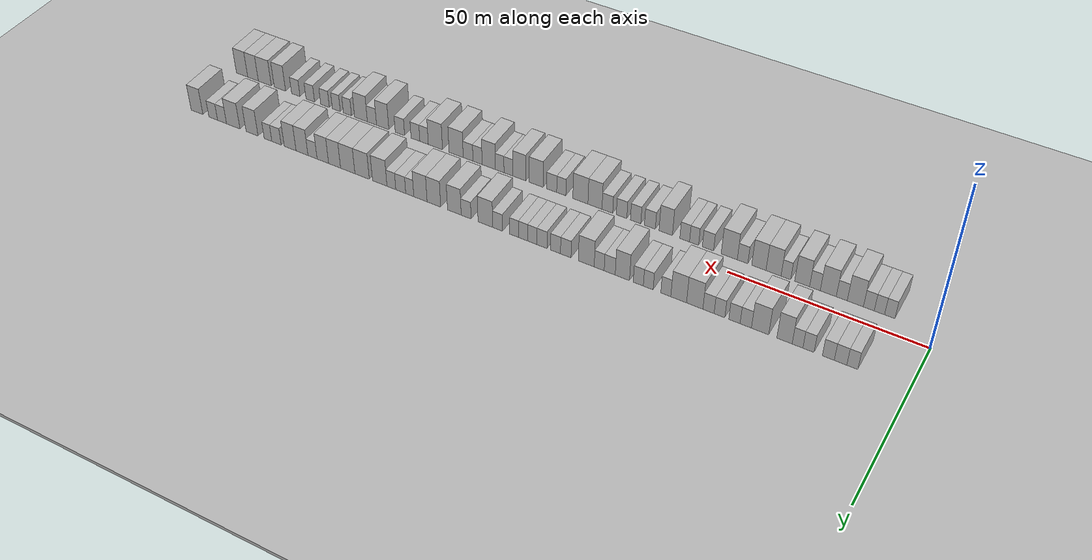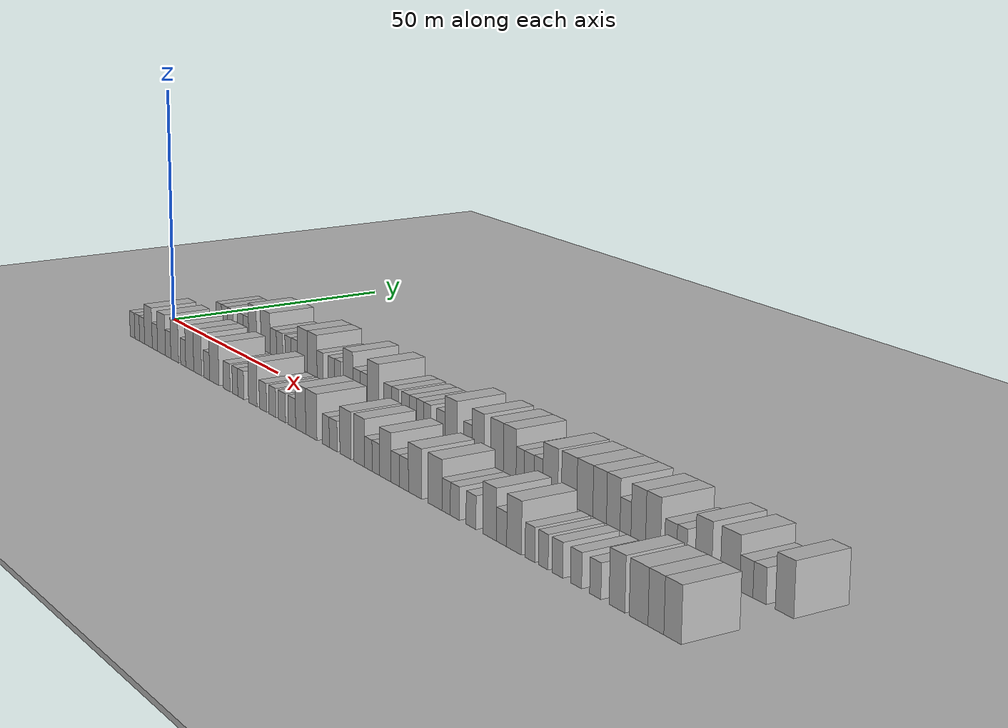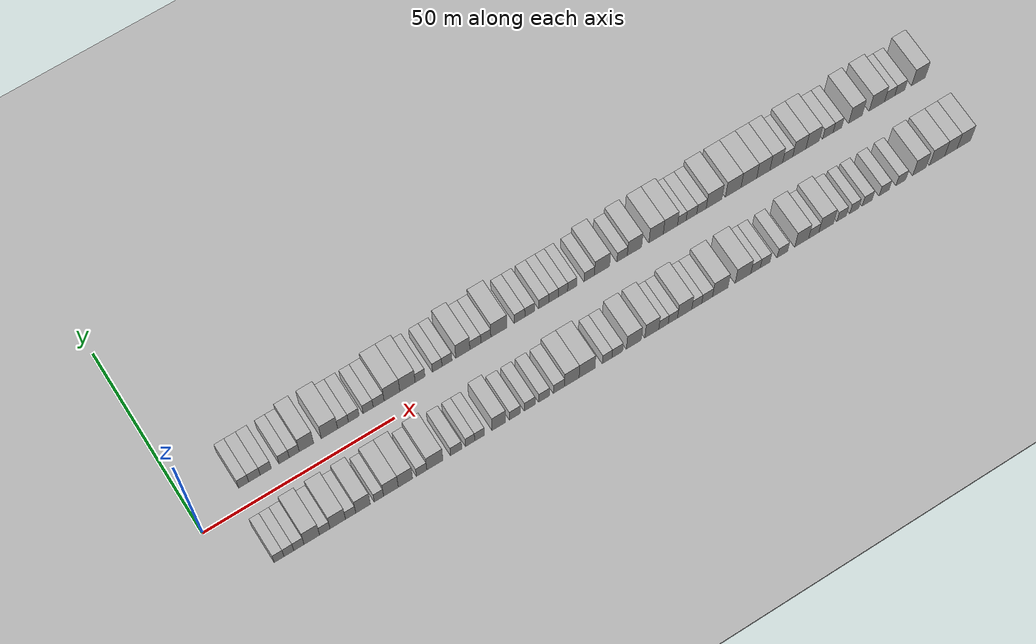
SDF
<?xml version="1.0" encoding="utf-8"?>

<sdf version="1.6">

   <world name="default">

      <gui fullscreen="0">

         <camera name="user_camera">

            <pose>-15 0 4.57585 0 0 0</pose>

            <view_controller>orbit</view_controller>

         </camera>

      </gui>

      <scene>

         <sky>

           <clouds>

             <speed>12</speed>

           </clouds>

         </sky>

         <ambient>0.4 0.4 0.4 1</ambient>

         <background>0.7 0.7 0.7 1</background>

         <shadows>1</shadows>

      </scene>

      <gravity>0 0 -9.8066</gravity>

      <magnetic_field>6e-06 2.3e-05 -4.2e-05</magnetic_field>

      <physics default="0" name="default_physics" type="ode">

         <ode>

            <solver>

               <type>quick</type>

               <iters>10</iters>

               <sor>1.0</sor>

               <use_dynamic_moi_rescaling>0</use_dynamic_moi_rescaling>

            </solver>

            <constraints>

               <cfm>0</cfm>

               <erp>0.2</erp>

               <contact_max_correcting_vel>100</contact_max_correcting_vel>

               <contact_surface_layer>0.001</contact_surface_layer>

            </constraints>

         </ode>

         <max_step_size>0.004</max_step_size>

         <real_time_factor>1</real_time_factor>

         <real_time_update_rate>250</real_time_update_rate>

      </physics>

      <light name="sun" type="directional">

         <cast_shadows>1</cast_shadows>

         <pose>0 0 10 0 0 0</pose>

         <diffuse>0.8 0.8 0.8 1</diffuse>

         <specular>0.2 0.2 0.2 1</specular>

         <attenuation>

            <range>1000</range>

            <constant>0.9</constant>

            <linear>0.01</linear>

            <quadratic>0.001</quadratic>

         </attenuation>

         <direction>-0.5 0.1 -0.9</direction>

      </light>

      <include>

         <name>ground_plane_1</name>

         <uri>model://HANNAS_ground_plane</uri>

         <pose>0 0 0  0 0 0</pose>

      </include>

      <include>

         <name>ground_plane_2</name>

         <uri>model://HANNAS_ground_plane</uri>

         <pose>100 0 0  0 0 0</pose>

      </include>

      <model name="building_1">

         <static>1</static>

         <pose frame="">13.3037 9.5000 0 0.000000 0.000000 1.570796</pose>

         <link name="link">

            <pose frame="">0 0 3.00 0 0 0</pose>

            <collision name="collision">

               <geometry>

                  <box>

                     <size>10.0000 2.6074 6.0000</size>

                  </box>

               </geometry>

               <max_contacts>10</max_contacts>

               <surface>

                  <contact>

                     <ode/>

                  </contact>

                  <bounce/>

                  <friction>

                     <torsional>

                        <ode/>

                     </torsional>

                     <ode/>

                  </friction>

               </surface>

            </collision>

            <visual name="visual">

               <cast_shadows>0</cast_shadows>

               <geometry>

                  <box>

                     <size>10.0000 2.6074 6.0000</size>

                  </box>

               </geometry>

               <material>

                  <script>

                     <uri>model://HANNAS_wall/materials/scripts</uri>

                     <uri>model://HANNAS_wall/materials/textures</uri>

                     <name>vrc/HANNAS_wall</name>

                  </script>

               </material>

            </visual>

            <self_collide>0</self_collide>

            <enable_wind>0</enable_wind>

            <kinematic>0</kinematic>

         </link>

      </model>

      <model name="building_2">

         <static>1</static>

         <pose frame="">16.0971 9.5000 0 0.000000 0.000000 1.570796</pose>

         <link name="link">

            <pose frame="">0 0 3.00 0 0 0</pose>

            <collision name="collision">

               <geometry>

                  <box>

                     <size>10.0000 2.9794 6.0000</size>

                  </box>

               </geometry>

               <max_contacts>10</max_contacts>

               <surface>

                  <contact>

                     <ode/>

                  </contact>

                  <bounce/>

                  <friction>

                     <torsional>

                        <ode/>

                     </torsional>

                     <ode/>

                  </friction>

               </surface>

            </collision>

            <visual name="visual">

               <cast_shadows>0</cast_shadows>

               <geometry>

                  <box>

                     <size>10.0000 2.9794 6.0000</size>

                  </box>

               </geometry>

               <material>

                  <script>

                     <uri>model://HANNAS_wall/materials/scripts</uri>

                     <uri>model://HANNAS_wall/materials/textures</uri>

                     <name>vrc/HANNAS_wall</name>

                  </script>

               </material>

            </visual>

            <self_collide>0</self_collide>

            <enable_wind>0</enable_wind>

            <kinematic>0</kinematic>

         </link>

      </model>

      <model name="building_3">

         <static>1</static>

         <pose frame="">19.0187 9.5000 0 0.000000 0.000000 1.570796</pose>

         <link name="link">

            <pose frame="">0 0 3.00 0 0 0</pose>

            <collision name="collision">

               <geometry>

                  <box>

                     <size>10.0000 2.8639 6.0000</size>

                  </box>

               </geometry>

               <max_contacts>10</max_contacts>

               <surface>

                  <contact>

                     <ode/>

                  </contact>

                  <bounce/>

                  <friction>

                     <torsional>

                        <ode/>

                     </torsional>

                     <ode/>

                  </friction>

               </surface>

            </collision>

            <visual name="visual">

               <cast_shadows>0</cast_shadows>

               <geometry>

                  <box>

                     <size>10.0000 2.8639 6.0000</size>

                  </box>

               </geometry>

               <material>

                  <script>

                     <uri>model://HANNAS_wall/materials/scripts</uri>

                     <uri>model://HANNAS_wall/materials/textures</uri>

                     <name>vrc/HANNAS_wall</name>

                  </script>

               </material>

            </visual>

            <self_collide>0</self_collide>

            <enable_wind>0</enable_wind>

            <kinematic>0</kinematic>

         </link>

      </model>

      <model name="building_4">

         <static>1</static>

         <pose frame="">23.7933 9.5000 0 0.000000 0.000000 1.570796</pose>

         <link name="link">

            <pose frame="">0 0 3.00 0 0 0</pose>

            <collision name="collision">

               <geometry>

                  <box>

                     <size>10.0000 2.6853 6.0000</size>

                  </box>

               </geometry>

               <max_contacts>10</max_contacts>

               <surface>

                  <contact>

                     <ode/>

                  </contact>

                  <bounce/>

                  <friction>

                     <torsional>

                        <ode/>

                     </torsional>

                     <ode/>

                  </friction>

               </surface>

            </collision>

            <visual name="visual">

               <cast_shadows>0</cast_shadows>

               <geometry>

                  <box>

                     <size>10.0000 2.6853 6.0000</size>

                  </box>

               </geometry>

               <material>

                  <script>

                     <uri>model://HANNAS_wall/materials/scripts</uri>

                     <uri>model://HANNAS_wall/materials/textures</uri>

                     <name>vrc/HANNAS_wall</name>

                  </script>

               </material>

            </visual>

            <self_collide>0</self_collide>

            <enable_wind>0</enable_wind>

            <kinematic>0</kinematic>

         </link>

      </model>

      <model name="building_5">

         <static>1</static>

         <pose frame="">26.4383 9.5000 0 0.000000 0.000000 1.570796</pose>

         <link name="link">

            <pose frame="">0 0 3.00 0 0 0</pose>

            <collision name="collision">

               <geometry>

                  <box>

                     <size>10.0000 2.6049 6.0000</size>

                  </box>

               </geometry>

               <max_contacts>10</max_contacts>

               <surface>

                  <contact>

                     <ode/>

                  </contact>

                  <bounce/>

                  <friction>

                     <torsional>

                        <ode/>

                     </torsional>

                     <ode/>

                  </friction>

               </surface>

            </collision>

            <visual name="visual">

               <cast_shadows>0</cast_shadows>

               <geometry>

                  <box>

                     <size>10.0000 2.6049 6.0000</size>

                  </box>

               </geometry>

               <material>

                  <script>

                     <uri>model://HANNAS_wall/materials/scripts</uri>

                     <uri>model://HANNAS_wall/materials/textures</uri>

                     <name>vrc/HANNAS_wall</name>

                  </script>

               </material>

            </visual>

            <self_collide>0</self_collide>

            <enable_wind>0</enable_wind>

            <kinematic>0</kinematic>

         </link>

      </model>

      <model name="building_6">

         <static>1</static>

         <pose frame="">29.6137 9.5000 0 0.000000 0.000000 1.570796</pose>

         <link name="link">

            <pose frame="">0 0 4.50 0 0 0</pose>

            <collision name="collision">

               <geometry>

                  <box>

                     <size>10.0000 3.7458 9.0000</size>

                  </box>

               </geometry>

               <max_contacts>10</max_contacts>

               <surface>

                  <contact>

                     <ode/>

                  </contact>

                  <bounce/>

                  <friction>

                     <torsional>

                        <ode/>

                     </torsional>

                     <ode/>

                  </friction>

               </surface>

            </collision>

            <visual name="visual">

               <cast_shadows>0</cast_shadows>

               <geometry>

                  <box>

                     <size>10.0000 3.7458 9.0000</size>

                  </box>

               </geometry>

               <material>

                  <script>

                     <uri>model://HANNAS_wall/materials/scripts</uri>

                     <uri>model://HANNAS_wall/materials/textures</uri>

                     <name>vrc/HANNAS_wall</name>

                  </script>

               </material>

            </visual>

            <self_collide>0</self_collide>

            <enable_wind>0</enable_wind>

            <kinematic>0</kinematic>

         </link>

      </model>

      <model name="building_7">

         <static>1</static>

         <pose frame="">35.6239 9.5000 0 0.000000 0.000000 1.570796</pose>

         <link name="link">

            <pose frame="">0 0 4.50 0 0 0</pose>

            <collision name="collision">

               <geometry>

                  <box>

                     <size>10.0000 4.2746 9.0000</size>

                  </box>

               </geometry>

               <max_contacts>10</max_contacts>

               <surface>

                  <contact>

                     <ode/>

                  </contact>

                  <bounce/>

                  <friction>

                     <torsional>

                        <ode/>

                     </torsional>

                     <ode/>

                  </friction>

               </surface>

            </collision>

            <visual name="visual">

               <cast_shadows>0</cast_shadows>

               <geometry>

                  <box>

                     <size>10.0000 4.2746 9.0000</size>

                  </box>

               </geometry>

               <material>

                  <script>

                     <uri>model://HANNAS_wall/materials/scripts</uri>

                     <uri>model://HANNAS_wall/materials/textures</uri>

                     <name>vrc/HANNAS_wall</name>

                  </script>

               </material>

            </visual>

            <self_collide>0</self_collide>

            <enable_wind>0</enable_wind>

            <kinematic>0</kinematic>

         </link>

      </model>

      <model name="building_8">

         <static>1</static>

         <pose frame="">39.1787 9.5000 0 0.000000 0.000000 1.570796</pose>

         <link name="link">

            <pose frame="">0 0 3.00 0 0 0</pose>

            <collision name="collision">

               <geometry>

                  <box>

                     <size>10.0000 2.8350 6.0000</size>

                  </box>

               </geometry>

               <max_contacts>10</max_contacts>

               <surface>

                  <contact>

                     <ode/>

                  </contact>

                  <bounce/>

                  <friction>

                     <torsional>

                        <ode/>

                     </torsional>

                     <ode/>

                  </friction>

               </surface>

            </collision>

            <visual name="visual">

               <cast_shadows>0</cast_shadows>

               <geometry>

                  <box>

                     <size>10.0000 2.8350 6.0000</size>

                  </box>

               </geometry>

               <material>

                  <script>

                     <uri>model://HANNAS_wall/materials/scripts</uri>

                     <uri>model://HANNAS_wall/materials/textures</uri>

                     <name>vrc/HANNAS_wall</name>

                  </script>

               </material>

            </visual>

            <self_collide>0</self_collide>

            <enable_wind>0</enable_wind>

            <kinematic>0</kinematic>

         </link>

      </model>

      <model name="building_9">

         <static>1</static>

         <pose frame="">42.0162 9.5000 0 0.000000 0.000000 1.570796</pose>

         <link name="link">

            <pose frame="">0 0 3.00 0 0 0</pose>

            <collision name="collision">

               <geometry>

                  <box>

                     <size>10.0000 2.8400 6.0000</size>

                  </box>

               </geometry>

               <max_contacts>10</max_contacts>

               <surface>

                  <contact>

                     <ode/>

                  </contact>

                  <bounce/>

                  <friction>

                     <torsional>

                        <ode/>

                     </torsional>

                     <ode/>

                  </friction>

               </surface>

            </collision>

            <visual name="visual">

               <cast_shadows>0</cast_shadows>

               <geometry>

                  <box>

                     <size>10.0000 2.8400 6.0000</size>

                  </box>

               </geometry>

               <material>

                  <script>

                     <uri>model://HANNAS_wall/materials/scripts</uri>

                     <uri>model://HANNAS_wall/materials/textures</uri>

                     <name>vrc/HANNAS_wall</name>

                  </script>

               </material>

            </visual>

            <self_collide>0</self_collide>

            <enable_wind>0</enable_wind>

            <kinematic>0</kinematic>

         </link>

      </model>

      <model name="building_10">

         <static>1</static>

         <pose frame="">45.7865 9.5000 0 0.000000 0.000000 1.570796</pose>

         <link name="link">

            <pose frame="">0 0 3.00 0 0 0</pose>

            <collision name="collision">

               <geometry>

                  <box>

                     <size>10.0000 2.7007 6.0000</size>

                  </box>

               </geometry>

               <max_contacts>10</max_contacts>

               <surface>

                  <contact>

                     <ode/>

                  </contact>

                  <bounce/>

                  <friction>

                     <torsional>

                        <ode/>

                     </torsional>

                     <ode/>

                  </friction>

               </surface>

            </collision>

            <visual name="visual">

               <cast_shadows>0</cast_shadows>

               <geometry>

                  <box>

                     <size>10.0000 2.7007 6.0000</size>

                  </box>

               </geometry>

               <material>

                  <script>

                     <uri>model://HANNAS_wall/materials/scripts</uri>

                     <uri>model://HANNAS_wall/materials/textures</uri>

                     <name>vrc/HANNAS_wall</name>

                  </script>

               </material>

            </visual>

            <self_collide>0</self_collide>

            <enable_wind>0</enable_wind>

            <kinematic>0</kinematic>

         </link>

      </model>

      <model name="building_11">

         <static>1</static>

         <pose frame="">48.5643 9.5000 0 0.000000 0.000000 1.570796</pose>

         <link name="link">

            <pose frame="">0 0 3.00 0 0 0</pose>

            <collision name="collision">

               <geometry>

                  <box>

                     <size>10.0000 2.8550 6.0000</size>

                  </box>

               </geometry>

               <max_contacts>10</max_contacts>

               <surface>

                  <contact>

                     <ode/>

                  </contact>

                  <bounce/>

                  <friction>

                     <torsional>

                        <ode/>

                     </torsional>

                     <ode/>

                  </friction>

               </surface>

            </collision>

            <visual name="visual">

               <cast_shadows>0</cast_shadows>

               <geometry>

                  <box>

                     <size>10.0000 2.8550 6.0000</size>

                  </box>

               </geometry>

               <material>

                  <script>

                     <uri>model://HANNAS_wall/materials/scripts</uri>

                     <uri>model://HANNAS_wall/materials/textures</uri>

                     <name>vrc/HANNAS_wall</name>

                  </script>

               </material>

            </visual>

            <self_collide>0</self_collide>

            <enable_wind>0</enable_wind>

            <kinematic>0</kinematic>

         </link>

      </model>

      <model name="building_12">

         <static>1</static>

         <pose frame="">52.0824 9.5000 0 0.000000 0.000000 1.570796</pose>

         <link name="link">

            <pose frame="">0 0 4.50 0 0 0</pose>

            <collision name="collision">

               <geometry>

                  <box>

                     <size>10.0000 4.1811 9.0000</size>

                  </box>

               </geometry>

               <max_contacts>10</max_contacts>

               <surface>

                  <contact>

                     <ode/>

                  </contact>

                  <bounce/>

                  <friction>

                     <torsional>

                        <ode/>

                     </torsional>

                     <ode/>

                  </friction>

               </surface>

            </collision>

            <visual name="visual">

               <cast_shadows>0</cast_shadows>

               <geometry>

                  <box>

                     <size>10.0000 4.1811 9.0000</size>

                  </box>

               </geometry>

               <material>

                  <script>

                     <uri>model://HANNAS_wall/materials/scripts</uri>

                     <uri>model://HANNAS_wall/materials/textures</uri>

                     <name>vrc/HANNAS_wall</name>

                  </script>

               </material>

            </visual>

            <self_collide>0</self_collide>

            <enable_wind>0</enable_wind>

            <kinematic>0</kinematic>

         </link>

      </model>

      <model name="building_13">

         <static>1</static>

         <pose frame="">56.2039 9.5000 0 0.000000 0.000000 1.570796</pose>

         <link name="link">

            <pose frame="">0 0 4.50 0 0 0</pose>

            <collision name="collision">

               <geometry>

                  <box>

                     <size>10.0000 4.0620 9.0000</size>

                  </box>

               </geometry>

               <max_contacts>10</max_contacts>

               <surface>

                  <contact>

                     <ode/>

                  </contact>

                  <bounce/>

                  <friction>

                     <torsional>

                        <ode/>

                     </torsional>

                     <ode/>

                  </friction>

               </surface>

            </collision>

            <visual name="visual">

               <cast_shadows>0</cast_shadows>

               <geometry>

                  <box>

                     <size>10.0000 4.0620 9.0000</size>

                  </box>

               </geometry>

               <material>

                  <script>

                     <uri>model://HANNAS_wall/materials/scripts</uri>

                     <uri>model://HANNAS_wall/materials/textures</uri>

                     <name>vrc/HANNAS_wall</name>

                  </script>

               </material>

            </visual>

            <self_collide>0</self_collide>

            <enable_wind>0</enable_wind>

            <kinematic>0</kinematic>

         </link>

      </model>

      <model name="building_14">

         <static>1</static>

         <pose frame="">59.5326 9.5000 0 0.000000 0.000000 1.570796</pose>

         <link name="link">

            <pose frame="">0 0 3.00 0 0 0</pose>

            <collision name="collision">

               <geometry>

                  <box>

                     <size>10.0000 2.5955 6.0000</size>

                  </box>

               </geometry>

               <max_contacts>10</max_contacts>

               <surface>

                  <contact>

                     <ode/>

                  </contact>

                  <bounce/>

                  <friction>

                     <torsional>

                        <ode/>

                     </torsional>

                     <ode/>

                  </friction>

               </surface>

            </collision>

            <visual name="visual">

               <cast_shadows>0</cast_shadows>

               <geometry>

                  <box>

                     <size>10.0000 2.5955 6.0000</size>

                  </box>

               </geometry>

               <material>

                  <script>

                     <uri>model://HANNAS_wall/materials/scripts</uri>

                     <uri>model://HANNAS_wall/materials/textures</uri>

                     <name>vrc/HANNAS_wall</name>

                  </script>

               </material>

            </visual>

            <self_collide>0</self_collide>

            <enable_wind>0</enable_wind>

            <kinematic>0</kinematic>

         </link>

      </model>

      <model name="building_15">

         <static>1</static>

         <pose frame="">64.1183 9.5000 0 0.000000 0.000000 1.570796</pose>

         <link name="link">

            <pose frame="">0 0 3.00 0 0 0</pose>

            <collision name="collision">

               <geometry>

                  <box>

                     <size>10.0000 2.5758 6.0000</size>

                  </box>

               </geometry>

               <max_contacts>10</max_contacts>

               <surface>

                  <contact>

                     <ode/>

                  </contact>

                  <bounce/>

                  <friction>

                     <torsional>

                        <ode/>

                     </torsional>

                     <ode/>

                  </friction>

               </surface>

            </collision>

            <visual name="visual">

               <cast_shadows>0</cast_shadows>

               <geometry>

                  <box>

                     <size>10.0000 2.5758 6.0000</size>

                  </box>

               </geometry>

               <material>

                  <script>

                     <uri>model://HANNAS_wall/materials/scripts</uri>

                     <uri>model://HANNAS_wall/materials/textures</uri>

                     <name>vrc/HANNAS_wall</name>

                  </script>

               </material>

            </visual>

            <self_collide>0</self_collide>

            <enable_wind>0</enable_wind>

            <kinematic>0</kinematic>

         </link>

      </model>

      <model name="building_16">

         <static>1</static>

         <pose frame="">66.7314 9.5000 0 0.000000 0.000000 1.570796</pose>

         <link name="link">

            <pose frame="">0 0 3.00 0 0 0</pose>

            <collision name="collision">

               <geometry>

                  <box>

                     <size>10.0000 2.6505 6.0000</size>

                  </box>

               </geometry>

               <max_contacts>10</max_contacts>

               <surface>

                  <contact>

                     <ode/>

                  </contact>

                  <bounce/>

                  <friction>

                     <torsional>

                        <ode/>

                     </torsional>

                     <ode/>

                  </friction>

               </surface>

            </collision>

            <visual name="visual">

               <cast_shadows>0</cast_shadows>

               <geometry>

                  <box>

                     <size>10.0000 2.6505 6.0000</size>

                  </box>

               </geometry>

               <material>

                  <script>

                     <uri>model://HANNAS_wall/materials/scripts</uri>

                     <uri>model://HANNAS_wall/materials/textures</uri>

                     <name>vrc/HANNAS_wall</name>

                  </script>

               </material>

            </visual>

            <self_collide>0</self_collide>

            <enable_wind>0</enable_wind>

            <kinematic>0</kinematic>

         </link>

      </model>

      <model name="building_17">

         <static>1</static>

         <pose frame="">70.9541 9.5000 0 0.000000 0.000000 1.570796</pose>

         <link name="link">

            <pose frame="">0 0 4.50 0 0 0</pose>

            <collision name="collision">

               <geometry>

                  <box>

                     <size>10.0000 3.7949 9.0000</size>

                  </box>

               </geometry>

               <max_contacts>10</max_contacts>

               <surface>

                  <contact>

                     <ode/>

                  </contact>

                  <bounce/>

                  <friction>

                     <torsional>

                        <ode/>

                     </torsional>

                     <ode/>

                  </friction>

               </surface>

            </collision>

            <visual name="visual">

               <cast_shadows>0</cast_shadows>

               <geometry>

                  <box>

                     <size>10.0000 3.7949 9.0000</size>

                  </box>

               </geometry>

               <material>

                  <script>

                     <uri>model://HANNAS_wall/materials/scripts</uri>

                     <uri>model://HANNAS_wall/materials/textures</uri>

                     <name>vrc/HANNAS_wall</name>

                  </script>

               </material>

            </visual>

            <self_collide>0</self_collide>

            <enable_wind>0</enable_wind>

            <kinematic>0</kinematic>

         </link>

      </model>

      <model name="building_18">

         <static>1</static>

         <pose frame="">74.3240 9.5000 0 0.000000 0.000000 1.570796</pose>

         <link name="link">

            <pose frame="">0 0 3.00 0 0 0</pose>

            <collision name="collision">

               <geometry>

                  <box>

                     <size>10.0000 2.9449 6.0000</size>

                  </box>

               </geometry>

               <max_contacts>10</max_contacts>

               <surface>

                  <contact>

                     <ode/>

                  </contact>

                  <bounce/>

                  <friction>

                     <torsional>

                        <ode/>

                     </torsional>

                     <ode/>

                  </friction>

               </surface>

            </collision>

            <visual name="visual">

               <cast_shadows>0</cast_shadows>

               <geometry>

                  <box>

                     <size>10.0000 2.9449 6.0000</size>

                  </box>

               </geometry>

               <material>

                  <script>

                     <uri>model://HANNAS_wall/materials/scripts</uri>

                     <uri>model://HANNAS_wall/materials/textures</uri>

                     <name>vrc/HANNAS_wall</name>

                  </script>

               </material>

            </visual>

            <self_collide>0</self_collide>

            <enable_wind>0</enable_wind>

            <kinematic>0</kinematic>

         </link>

      </model>

      <model name="building_19">

         <static>1</static>

         <pose frame="">77.1398 9.5000 0 0.000000 0.000000 1.570796</pose>

         <link name="link">

            <pose frame="">0 0 3.00 0 0 0</pose>

            <collision name="collision">

               <geometry>

                  <box>

                     <size>10.0000 2.6867 6.0000</size>

                  </box>

               </geometry>

               <max_contacts>10</max_contacts>

               <surface>

                  <contact>

                     <ode/>

                  </contact>

                  <bounce/>

                  <friction>

                     <torsional>

                        <ode/>

                     </torsional>

                     <ode/>

                  </friction>

               </surface>

            </collision>

            <visual name="visual">

               <cast_shadows>0</cast_shadows>

               <geometry>

                  <box>

                     <size>10.0000 2.6867 6.0000</size>

                  </box>

               </geometry>

               <material>

                  <script>

                     <uri>model://HANNAS_wall/materials/scripts</uri>

                     <uri>model://HANNAS_wall/materials/textures</uri>

                     <name>vrc/HANNAS_wall</name>

                  </script>

               </material>

            </visual>

            <self_collide>0</self_collide>

            <enable_wind>0</enable_wind>

            <kinematic>0</kinematic>

         </link>

      </model>

      <model name="building_20">

         <static>1</static>

         <pose frame="">80.6303 9.5000 0 0.000000 0.000000 1.570796</pose>

         <link name="link">

            <pose frame="">0 0 4.50 0 0 0</pose>

            <collision name="collision">

               <geometry>

                  <box>

                     <size>10.0000 4.2942 9.0000</size>

                  </box>

               </geometry>

               <max_contacts>10</max_contacts>

               <surface>

                  <contact>

                     <ode/>

                  </contact>

                  <bounce/>

                  <friction>

                     <torsional>

                        <ode/>

                     </torsional>

                     <ode/>

                  </friction>

               </surface>

            </collision>

            <visual name="visual">

               <cast_shadows>0</cast_shadows>

               <geometry>

                  <box>

                     <size>10.0000 4.2942 9.0000</size>

                  </box>

               </geometry>

               <material>

                  <script>

                     <uri>model://HANNAS_wall/materials/scripts</uri>

                     <uri>model://HANNAS_wall/materials/textures</uri>

                     <name>vrc/HANNAS_wall</name>

                  </script>

               </material>

            </visual>

            <self_collide>0</self_collide>

            <enable_wind>0</enable_wind>

            <kinematic>0</kinematic>

         </link>

      </model>

      <model name="building_21">

         <static>1</static>

         <pose frame="">86.2190 9.5000 0 0.000000 0.000000 1.570796</pose>

         <link name="link">

            <pose frame="">0 0 3.00 0 0 0</pose>

            <collision name="collision">

               <geometry>

                  <box>

                     <size>10.0000 2.8831 6.0000</size>

                  </box>

               </geometry>

               <max_contacts>10</max_contacts>

               <surface>

                  <contact>

                     <ode/>

                  </contact>

                  <bounce/>

                  <friction>

                     <torsional>

                        <ode/>

                     </torsional>

                     <ode/>

                  </friction>

               </surface>

            </collision>

            <visual name="visual">

               <cast_shadows>0</cast_shadows>

               <geometry>

                  <box>

                     <size>10.0000 2.8831 6.0000</size>

                  </box>

               </geometry>

               <material>

                  <script>

                     <uri>model://HANNAS_wall/materials/scripts</uri>

                     <uri>model://HANNAS_wall/materials/textures</uri>

                     <name>vrc/HANNAS_wall</name>

                  </script>

               </material>

            </visual>

            <self_collide>0</self_collide>

            <enable_wind>0</enable_wind>

            <kinematic>0</kinematic>

         </link>

      </model>

      <model name="building_22">

         <static>1</static>

         <pose frame="">89.0271 9.5000 0 0.000000 0.000000 1.570796</pose>

         <link name="link">

            <pose frame="">0 0 3.00 0 0 0</pose>

            <collision name="collision">

               <geometry>

                  <box>

                     <size>10.0000 2.7332 6.0000</size>

                  </box>

               </geometry>

               <max_contacts>10</max_contacts>

               <surface>

                  <contact>

                     <ode/>

                  </contact>

                  <bounce/>

                  <friction>

                     <torsional>

                        <ode/>

                     </torsional>

                     <ode/>

                  </friction>

               </surface>

            </collision>

            <visual name="visual">

               <cast_shadows>0</cast_shadows>

               <geometry>

                  <box>

                     <size>10.0000 2.7332 6.0000</size>

                  </box>

               </geometry>

               <material>

                  <script>

                     <uri>model://HANNAS_wall/materials/scripts</uri>

                     <uri>model://HANNAS_wall/materials/textures</uri>

                     <name>vrc/HANNAS_wall</name>

                  </script>

               </material>

            </visual>

            <self_collide>0</self_collide>

            <enable_wind>0</enable_wind>

            <kinematic>0</kinematic>

         </link>

      </model>

      <model name="building_23">

         <static>1</static>

         <pose frame="">92.7909 9.5000 0 0.000000 0.000000 1.570796</pose>

         <link name="link">

            <pose frame="">0 0 3.00 0 0 0</pose>

            <collision name="collision">

               <geometry>

                  <box>

                     <size>10.0000 2.7945 6.0000</size>

                  </box>

               </geometry>

               <max_contacts>10</max_contacts>

               <surface>

                  <contact>

                     <ode/>

                  </contact>

                  <bounce/>

                  <friction>

                     <torsional>

                        <ode/>

                     </torsional>

                     <ode/>

                  </friction>

               </surface>

            </collision>

            <visual name="visual">

               <cast_shadows>0</cast_shadows>

               <geometry>

                  <box>

                     <size>10.0000 2.7945 6.0000</size>

                  </box>

               </geometry>

               <material>

                  <script>

                     <uri>model://HANNAS_wall/materials/scripts</uri>

                     <uri>model://HANNAS_wall/materials/textures</uri>

                     <name>vrc/HANNAS_wall</name>

                  </script>

               </material>

            </visual>

            <self_collide>0</self_collide>

            <enable_wind>0</enable_wind>

            <kinematic>0</kinematic>

         </link>

      </model>

      <model name="building_24">

         <static>1</static>

         <pose frame="">95.4669 9.5000 0 0.000000 0.000000 1.570796</pose>

         <link name="link">

            <pose frame="">0 0 3.00 0 0 0</pose>

            <collision name="collision">

               <geometry>

                  <box>

                     <size>10.0000 2.5574 6.0000</size>

                  </box>

               </geometry>

               <max_contacts>10</max_contacts>

               <surface>

                  <contact>

                     <ode/>

                  </contact>

                  <bounce/>

                  <friction>

                     <torsional>

                        <ode/>

                     </torsional>

                     <ode/>

                  </friction>

               </surface>

            </collision>

            <visual name="visual">

               <cast_shadows>0</cast_shadows>

               <geometry>

                  <box>

                     <size>10.0000 2.5574 6.0000</size>

                  </box>

               </geometry>

               <material>

                  <script>

                     <uri>model://HANNAS_wall/materials/scripts</uri>

                     <uri>model://HANNAS_wall/materials/textures</uri>

                     <name>vrc/HANNAS_wall</name>

                  </script>

               </material>

            </visual>

            <self_collide>0</self_collide>

            <enable_wind>0</enable_wind>

            <kinematic>0</kinematic>

         </link>

      </model>

      <model name="building_25">

         <static>1</static>

         <pose frame="">98.0242 9.5000 0 0.000000 0.000000 1.570796</pose>

         <link name="link">

            <pose frame="">0 0 3.00 0 0 0</pose>

            <collision name="collision">

               <geometry>

                  <box>

                     <size>10.0000 2.5574 6.0000</size>

                  </box>

               </geometry>

               <max_contacts>10</max_contacts>

               <surface>

                  <contact>

                     <ode/>

                  </contact>

                  <bounce/>

                  <friction>

                     <torsional>

                        <ode/>

                     </torsional>

                     <ode/>

                  </friction>

               </surface>

            </collision>

            <visual name="visual">

               <cast_shadows>0</cast_shadows>

               <geometry>

                  <box>

                     <size>10.0000 2.5574 6.0000</size>

                  </box>

               </geometry>

               <material>

                  <script>

                     <uri>model://HANNAS_wall/materials/scripts</uri>

                     <uri>model://HANNAS_wall/materials/textures</uri>

                     <name>vrc/HANNAS_wall</name>

                  </script>

               </material>

            </visual>

            <self_collide>0</self_collide>

            <enable_wind>0</enable_wind>

            <kinematic>0</kinematic>

         </link>

      </model>

      <model name="building_26">

         <static>1</static>

         <pose frame="">100.5548 9.5000 0 0.000000 0.000000 1.570796</pose>

         <link name="link">

            <pose frame="">0 0 3.00 0 0 0</pose>

            <collision name="collision">

               <geometry>

                  <box>

                     <size>10.0000 2.5036 6.0000</size>

                  </box>

               </geometry>

               <max_contacts>10</max_contacts>

               <surface>

                  <contact>

                     <ode/>

                  </contact>

                  <bounce/>

                  <friction>

                     <torsional>

                        <ode/>

                     </torsional>

                     <ode/>

                  </friction>

               </surface>

            </collision>

            <visual name="visual">

               <cast_shadows>0</cast_shadows>

               <geometry>

                  <box>

                     <size>10.0000 2.5036 6.0000</size>

                  </box>

               </geometry>

               <material>

                  <script>

                     <uri>model://HANNAS_wall/materials/scripts</uri>

                     <uri>model://HANNAS_wall/materials/textures</uri>

                     <name>vrc/HANNAS_wall</name>

                  </script>

               </material>

            </visual>

            <self_collide>0</self_collide>

            <enable_wind>0</enable_wind>

            <kinematic>0</kinematic>

         </link>

      </model>

      <model name="building_27">

         <static>1</static>

         <pose frame="">105.2196 9.5000 0 0.000000 0.000000 1.570796</pose>

         <link name="link">

            <pose frame="">0 0 3.00 0 0 0</pose>

            <collision name="collision">

               <geometry>

                  <box>

                     <size>10.0000 2.8261 6.0000</size>

                  </box>

               </geometry>

               <max_contacts>10</max_contacts>

               <surface>

                  <contact>

                     <ode/>

                  </contact>

                  <bounce/>

                  <friction>

                     <torsional>

                        <ode/>

                     </torsional>

                     <ode/>

                  </friction>

               </surface>

            </collision>

            <visual name="visual">

               <cast_shadows>0</cast_shadows>

               <geometry>

                  <box>

                     <size>10.0000 2.8261 6.0000</size>

                  </box>

               </geometry>

               <material>

                  <script>

                     <uri>model://HANNAS_wall/materials/scripts</uri>

                     <uri>model://HANNAS_wall/materials/textures</uri>

                     <name>vrc/HANNAS_wall</name>

                  </script>

               </material>

            </visual>

            <self_collide>0</self_collide>

            <enable_wind>0</enable_wind>

            <kinematic>0</kinematic>

         </link>

      </model>

      <model name="building_28">

         <static>1</static>

         <pose frame="">108.7303 9.5000 0 0.000000 0.000000 1.570796</pose>

         <link name="link">

            <pose frame="">0 0 4.50 0 0 0</pose>

            <collision name="collision">

               <geometry>

                  <box>

                     <size>10.0000 4.1952 9.0000</size>

                  </box>

               </geometry>

               <max_contacts>10</max_contacts>

               <surface>

                  <contact>

                     <ode/>

                  </contact>

                  <bounce/>

                  <friction>

                     <torsional>

                        <ode/>

                     </torsional>

                     <ode/>

                  </friction>

               </surface>

            </collision>

            <visual name="visual">

               <cast_shadows>0</cast_shadows>

               <geometry>

                  <box>

                     <size>10.0000 4.1952 9.0000</size>

                  </box>

               </geometry>

               <material>

                  <script>

                     <uri>model://HANNAS_wall/materials/scripts</uri>

                     <uri>model://HANNAS_wall/materials/textures</uri>

                     <name>vrc/HANNAS_wall</name>

                  </script>

               </material>

            </visual>

            <self_collide>0</self_collide>

            <enable_wind>0</enable_wind>

            <kinematic>0</kinematic>

         </link>

      </model>

      <model name="building_29">

         <static>1</static>

         <pose frame="">114.2613 9.5000 0 0.000000 0.000000 1.570796</pose>

         <link name="link">

            <pose frame="">0 0 3.00 0 0 0</pose>

            <collision name="collision">

               <geometry>

                  <box>

                     <size>10.0000 2.8669 6.0000</size>

                  </box>

               </geometry>

               <max_contacts>10</max_contacts>

               <surface>

                  <contact>

                     <ode/>

                  </contact>

                  <bounce/>

                  <friction>

                     <torsional>

                        <ode/>

                     </torsional>

                     <ode/>

                  </friction>

               </surface>

            </collision>

            <visual name="visual">

               <cast_shadows>0</cast_shadows>

               <geometry>

                  <box>

                     <size>10.0000 2.8669 6.0000</size>

                  </box>

               </geometry>

               <material>

                  <script>

                     <uri>model://HANNAS_wall/materials/scripts</uri>

                     <uri>model://HANNAS_wall/materials/textures</uri>

                     <name>vrc/HANNAS_wall</name>

                  </script>

               </material>

            </visual>

            <self_collide>0</self_collide>

            <enable_wind>0</enable_wind>

            <kinematic>0</kinematic>

         </link>

      </model>

      <model name="building_30">

         <static>1</static>

         <pose frame="">117.6817 9.5000 0 0.000000 0.000000 1.570796</pose>

         <link name="link">

            <pose frame="">0 0 4.50 0 0 0</pose>

            <collision name="collision">

               <geometry>

                  <box>

                     <size>10.0000 3.9738 9.0000</size>

                  </box>

               </geometry>

               <max_contacts>10</max_contacts>

               <surface>

                  <contact>

                     <ode/>

                  </contact>

                  <bounce/>

                  <friction>

                     <torsional>

                        <ode/>

                     </torsional>

                     <ode/>

                  </friction>

               </surface>

            </collision>

            <visual name="visual">

               <cast_shadows>0</cast_shadows>

               <geometry>

                  <box>

                     <size>10.0000 3.9738 9.0000</size>

                  </box>

               </geometry>

               <material>

                  <script>

                     <uri>model://HANNAS_wall/materials/scripts</uri>

                     <uri>model://HANNAS_wall/materials/textures</uri>

                     <name>vrc/HANNAS_wall</name>

                  </script>

               </material>

            </visual>

            <self_collide>0</self_collide>

            <enable_wind>0</enable_wind>

            <kinematic>0</kinematic>

         </link>

      </model>

      <model name="building_31">

         <static>1</static>

         <pose frame="">123.6691 9.5000 0 0.000000 0.000000 1.570796</pose>

         <link name="link">

            <pose frame="">0 0 4.50 0 0 0</pose>

            <collision name="collision">

               <geometry>

                  <box>

                     <size>10.0000 4.0010 9.0000</size>

                  </box>

               </geometry>

               <max_contacts>10</max_contacts>

               <surface>

                  <contact>

                     <ode/>

                  </contact>

                  <bounce/>

                  <friction>

                     <torsional>

                        <ode/>

                     </torsional>

                     <ode/>

                  </friction>

               </surface>

            </collision>

            <visual name="visual">

               <cast_shadows>0</cast_shadows>

               <geometry>

                  <box>

                     <size>10.0000 4.0010 9.0000</size>

                  </box>

               </geometry>

               <material>

                  <script>

                     <uri>model://HANNAS_wall/materials/scripts</uri>

                     <uri>model://HANNAS_wall/materials/textures</uri>

                     <name>vrc/HANNAS_wall</name>

                  </script>

               </material>

            </visual>

            <self_collide>0</self_collide>

            <enable_wind>0</enable_wind>

            <kinematic>0</kinematic>

         </link>

      </model>

      <model name="building_32">

         <static>1</static>

         <pose frame="">127.6416 9.5000 0 0.000000 0.000000 1.570796</pose>

         <link name="link">

            <pose frame="">0 0 4.50 0 0 0</pose>

            <collision name="collision">

               <geometry>

                  <box>

                     <size>10.0000 3.9440 9.0000</size>

                  </box>

               </geometry>

               <max_contacts>10</max_contacts>

               <surface>

                  <contact>

                     <ode/>

                  </contact>

                  <bounce/>

                  <friction>

                     <torsional>

                        <ode/>

                     </torsional>

                     <ode/>

                  </friction>

               </surface>

            </collision>

            <visual name="visual">

               <cast_shadows>0</cast_shadows>

               <geometry>

                  <box>

                     <size>10.0000 3.9440 9.0000</size>

                  </box>

               </geometry>

               <material>

                  <script>

                     <uri>model://HANNAS_wall/materials/scripts</uri>

                     <uri>model://HANNAS_wall/materials/textures</uri>

                     <name>vrc/HANNAS_wall</name>

                  </script>

               </material>

            </visual>

            <self_collide>0</self_collide>

            <enable_wind>0</enable_wind>

            <kinematic>0</kinematic>

         </link>

      </model>

      <model name="building_33">

         <static>1</static>

         <pose frame="">130.8150 9.5000 0 0.000000 0.000000 1.570796</pose>

         <link name="link">

            <pose frame="">0 0 3.00 0 0 0</pose>

            <collision name="collision">

               <geometry>

                  <box>

                     <size>10.0000 2.4028 6.0000</size>

                  </box>

               </geometry>

               <max_contacts>10</max_contacts>

               <surface>

                  <contact>

                     <ode/>

                  </contact>

                  <bounce/>

                  <friction>

                     <torsional>

                        <ode/>

                     </torsional>

                     <ode/>

                  </friction>

               </surface>

            </collision>

            <visual name="visual">

               <cast_shadows>0</cast_shadows>

               <geometry>

                  <box>

                     <size>10.0000 2.4028 6.0000</size>

                  </box>

               </geometry>

               <material>

                  <script>

                     <uri>model://HANNAS_wall/materials/scripts</uri>

                     <uri>model://HANNAS_wall/materials/textures</uri>

                     <name>vrc/HANNAS_wall</name>

                  </script>

               </material>

            </visual>

            <self_collide>0</self_collide>

            <enable_wind>0</enable_wind>

            <kinematic>0</kinematic>

         </link>

      </model>

      <model name="building_34">

         <static>1</static>

         <pose frame="">133.5096 9.5000 0 0.000000 0.000000 1.570796</pose>

         <link name="link">

            <pose frame="">0 0 3.00 0 0 0</pose>

            <collision name="collision">

               <geometry>

                  <box>

                     <size>10.0000 2.9864 6.0000</size>

                  </box>

               </geometry>

               <max_contacts>10</max_contacts>

               <surface>

                  <contact>

                     <ode/>

                  </contact>

                  <bounce/>

                  <friction>

                     <torsional>

                        <ode/>

                     </torsional>

                     <ode/>

                  </friction>

               </surface>

            </collision>

            <visual name="visual">

               <cast_shadows>0</cast_shadows>

               <geometry>

                  <box>

                     <size>10.0000 2.9864 6.0000</size>

                  </box>

               </geometry>

               <material>

                  <script>

                     <uri>model://HANNAS_wall/materials/scripts</uri>

                     <uri>model://HANNAS_wall/materials/textures</uri>

                     <name>vrc/HANNAS_wall</name>

                  </script>

               </material>

            </visual>

            <self_collide>0</self_collide>

            <enable_wind>0</enable_wind>

            <kinematic>0</kinematic>

         </link>

      </model>

      <model name="building_35">

         <static>1</static>

         <pose frame="">136.3296 9.5000 0 0.000000 0.000000 1.570796</pose>

         <link name="link">

            <pose frame="">0 0 3.00 0 0 0</pose>

            <collision name="collision">

               <geometry>

                  <box>

                     <size>10.0000 2.6536 6.0000</size>

                  </box>

               </geometry>

               <max_contacts>10</max_contacts>

               <surface>

                  <contact>

                     <ode/>

                  </contact>

                  <bounce/>

                  <friction>

                     <torsional>

                        <ode/>

                     </torsional>

                     <ode/>

                  </friction>

               </surface>

            </collision>

            <visual name="visual">

               <cast_shadows>0</cast_shadows>

               <geometry>

                  <box>

                     <size>10.0000 2.6536 6.0000</size>

                  </box>

               </geometry>

               <material>

                  <script>

                     <uri>model://HANNAS_wall/materials/scripts</uri>

                     <uri>model://HANNAS_wall/materials/textures</uri>

                     <name>vrc/HANNAS_wall</name>

                  </script>

               </material>

            </visual>

            <self_collide>0</self_collide>

            <enable_wind>0</enable_wind>

            <kinematic>0</kinematic>

         </link>

      </model>

      <model name="building_36">

         <static>1</static>

         <pose frame="">139.8455 9.5000 0 0.000000 0.000000 1.570796</pose>

         <link name="link">

            <pose frame="">0 0 4.50 0 0 0</pose>

            <collision name="collision">

               <geometry>

                  <box>

                     <size>10.0000 4.3783 9.0000</size>

                  </box>

               </geometry>

               <max_contacts>10</max_contacts>

               <surface>

                  <contact>

                     <ode/>

                  </contact>

                  <bounce/>

                  <friction>

                     <torsional>

                        <ode/>

                     </torsional>

                     <ode/>

                  </friction>

               </surface>

            </collision>

            <visual name="visual">

               <cast_shadows>0</cast_shadows>

               <geometry>

                  <box>

                     <size>10.0000 4.3783 9.0000</size>

                  </box>

               </geometry>

               <material>

                  <script>

                     <uri>model://HANNAS_wall/materials/scripts</uri>

                     <uri>model://HANNAS_wall/materials/textures</uri>

                     <name>vrc/HANNAS_wall</name>

                  </script>

               </material>

            </visual>

            <self_collide>0</self_collide>

            <enable_wind>0</enable_wind>

            <kinematic>0</kinematic>

         </link>

      </model>

      <model name="building_37">

         <static>1</static>

         <pose frame="">145.2298 9.5000 0 0.000000 0.000000 1.570796</pose>

         <link name="link">

            <pose frame="">0 0 4.50 0 0 0</pose>

            <collision name="collision">

               <geometry>

                  <box>

                     <size>10.0000 4.3902 9.0000</size>

                  </box>

               </geometry>

               <max_contacts>10</max_contacts>

               <surface>

                  <contact>

                     <ode/>

                  </contact>

                  <bounce/>

                  <friction>

                     <torsional>

                        <ode/>

                     </torsional>

                     <ode/>

                  </friction>

               </surface>

            </collision>

            <visual name="visual">

               <cast_shadows>0</cast_shadows>

               <geometry>

                  <box>

                     <size>10.0000 4.3902 9.0000</size>

                  </box>

               </geometry>

               <material>

                  <script>

                     <uri>model://HANNAS_wall/materials/scripts</uri>

                     <uri>model://HANNAS_wall/materials/textures</uri>

                     <name>vrc/HANNAS_wall</name>

                  </script>

               </material>

            </visual>

            <self_collide>0</self_collide>

            <enable_wind>0</enable_wind>

            <kinematic>0</kinematic>

         </link>

      </model>

      <model name="building_38">

         <static>1</static>

         <pose frame="">149.6399 9.5000 0 0.000000 0.000000 1.570796</pose>

         <link name="link">

            <pose frame="">0 0 4.50 0 0 0</pose>

            <collision name="collision">

               <geometry>

                  <box>

                     <size>10.0000 4.4301 9.0000</size>

                  </box>

               </geometry>

               <max_contacts>10</max_contacts>

               <surface>

                  <contact>

                     <ode/>

                  </contact>

                  <bounce/>

                  <friction>

                     <torsional>

                        <ode/>

                     </torsional>

                     <ode/>

                  </friction>

               </surface>

            </collision>

            <visual name="visual">

               <cast_shadows>0</cast_shadows>

               <geometry>

                  <box>

                     <size>10.0000 4.4301 9.0000</size>

                  </box>

               </geometry>

               <material>

                  <script>

                     <uri>model://HANNAS_wall/materials/scripts</uri>

                     <uri>model://HANNAS_wall/materials/textures</uri>

                     <name>vrc/HANNAS_wall</name>

                  </script>

               </material>

            </visual>

            <self_collide>0</self_collide>

            <enable_wind>0</enable_wind>

            <kinematic>0</kinematic>

         </link>

      </model>

      <model name="building_39">

         <static>1</static>

         <pose frame="">153.7185 9.5000 0 0.000000 0.000000 1.570796</pose>

         <link name="link">

            <pose frame="">0 0 4.50 0 0 0</pose>

            <collision name="collision">

               <geometry>

                  <box>

                     <size>10.0000 3.7272 9.0000</size>

                  </box>

               </geometry>

               <max_contacts>10</max_contacts>

               <surface>

                  <contact>

                     <ode/>

                  </contact>

                  <bounce/>

                  <friction>

                     <torsional>

                        <ode/>

                     </torsional>

                     <ode/>

                  </friction>

               </surface>

            </collision>

            <visual name="visual">

               <cast_shadows>0</cast_shadows>

               <geometry>

                  <box>

                     <size>10.0000 3.7272 9.0000</size>

                  </box>

               </geometry>

               <material>

                  <script>

                     <uri>model://HANNAS_wall/materials/scripts</uri>

                     <uri>model://HANNAS_wall/materials/textures</uri>

                     <name>vrc/HANNAS_wall</name>

                  </script>

               </material>

            </visual>

            <self_collide>0</self_collide>

            <enable_wind>0</enable_wind>

            <kinematic>0</kinematic>

         </link>

      </model>

      <model name="building_40">

         <static>1</static>

         <pose frame="">157.3882 9.5000 0 0.000000 0.000000 1.570796</pose>

         <link name="link">

            <pose frame="">0 0 4.50 0 0 0</pose>

            <collision name="collision">

               <geometry>

                  <box>

                     <size>10.0000 3.6120 9.0000</size>

                  </box>

               </geometry>

               <max_contacts>10</max_contacts>

               <surface>

                  <contact>

                     <ode/>

                  </contact>

                  <bounce/>

                  <friction>

                     <torsional>

                        <ode/>

                     </torsional>

                     <ode/>

                  </friction>

               </surface>

            </collision>

            <visual name="visual">

               <cast_shadows>0</cast_shadows>

               <geometry>

                  <box>

                     <size>10.0000 3.6120 9.0000</size>

                  </box>

               </geometry>

               <material>

                  <script>

                     <uri>model://HANNAS_wall/materials/scripts</uri>

                     <uri>model://HANNAS_wall/materials/textures</uri>

                     <name>vrc/HANNAS_wall</name>

                  </script>

               </material>

            </visual>

            <self_collide>0</self_collide>

            <enable_wind>0</enable_wind>

            <kinematic>0</kinematic>

         </link>

      </model>

      <model name="building_41">

         <static>1</static>

         <pose frame="">160.6313 9.5000 0 0.000000 0.000000 1.570796</pose>

         <link name="link">

            <pose frame="">0 0 3.00 0 0 0</pose>

            <collision name="collision">

               <geometry>

                  <box>

                     <size>10.0000 2.8742 6.0000</size>

                  </box>

               </geometry>

               <max_contacts>10</max_contacts>

               <surface>

                  <contact>

                     <ode/>

                  </contact>

                  <bounce/>

                  <friction>

                     <torsional>

                        <ode/>

                     </torsional>

                     <ode/>

                  </friction>

               </surface>

            </collision>

            <visual name="visual">

               <cast_shadows>0</cast_shadows>

               <geometry>

                  <box>

                     <size>10.0000 2.8742 6.0000</size>

                  </box>

               </geometry>

               <material>

                  <script>

                     <uri>model://HANNAS_wall/materials/scripts</uri>

                     <uri>model://HANNAS_wall/materials/textures</uri>

                     <name>vrc/HANNAS_wall</name>

                  </script>

               </material>

            </visual>

            <self_collide>0</self_collide>

            <enable_wind>0</enable_wind>

            <kinematic>0</kinematic>

         </link>

      </model>

      <model name="building_42">

         <static>1</static>

         <pose frame="">163.9559 9.5000 0 0.000000 0.000000 1.570796</pose>

         <link name="link">

            <pose frame="">0 0 4.50 0 0 0</pose>

            <collision name="collision">

               <geometry>

                  <box>

                     <size>10.0000 3.7749 9.0000</size>

                  </box>

               </geometry>

               <max_contacts>10</max_contacts>

               <surface>

                  <contact>

                     <ode/>

                  </contact>

                  <bounce/>

                  <friction>

                     <torsional>

                        <ode/>

                     </torsional>

                     <ode/>

                  </friction>

               </surface>

            </collision>

            <visual name="visual">

               <cast_shadows>0</cast_shadows>

               <geometry>

                  <box>

                     <size>10.0000 3.7749 9.0000</size>

                  </box>

               </geometry>

               <material>

                  <script>

                     <uri>model://HANNAS_wall/materials/scripts</uri>

                     <uri>model://HANNAS_wall/materials/textures</uri>

                     <name>vrc/HANNAS_wall</name>

                  </script>

               </material>

            </visual>

            <self_collide>0</self_collide>

            <enable_wind>0</enable_wind>

            <kinematic>0</kinematic>

         </link>

      </model>

      <model name="building_43">

         <static>1</static>

         <pose frame="">167.7307 9.5000 0 0.000000 0.000000 1.570796</pose>

         <link name="link">

            <pose frame="">0 0 4.50 0 0 0</pose>

            <collision name="collision">

               <geometry>

                  <box>

                     <size>10.0000 3.7747 9.0000</size>

                  </box>

               </geometry>

               <max_contacts>10</max_contacts>

               <surface>

                  <contact>

                     <ode/>

                  </contact>

                  <bounce/>

                  <friction>

                     <torsional>

                        <ode/>

                     </torsional>

                     <ode/>

                  </friction>

               </surface>

            </collision>

            <visual name="visual">

               <cast_shadows>0</cast_shadows>

               <geometry>

                  <box>

                     <size>10.0000 3.7747 9.0000</size>

                  </box>

               </geometry>

               <material>

                  <script>

                     <uri>model://HANNAS_wall/materials/scripts</uri>

                     <uri>model://HANNAS_wall/materials/textures</uri>

                     <name>vrc/HANNAS_wall</name>

                  </script>

               </material>

            </visual>

            <self_collide>0</self_collide>

            <enable_wind>0</enable_wind>

            <kinematic>0</kinematic>

         </link>

      </model>

      <model name="building_44">

         <static>1</static>

         <pose frame="">172.1160 9.5000 0 0.000000 0.000000 1.570796</pose>

         <link name="link">

            <pose frame="">0 0 3.00 0 0 0</pose>

            <collision name="collision">

               <geometry>

                  <box>

                     <size>10.0000 2.9960 6.0000</size>

                  </box>

               </geometry>

               <max_contacts>10</max_contacts>

               <surface>

                  <contact>

                     <ode/>

                  </contact>

                  <bounce/>

                  <friction>

                     <torsional>

                        <ode/>

                     </torsional>

                     <ode/>

                  </friction>

               </surface>

            </collision>

            <visual name="visual">

               <cast_shadows>0</cast_shadows>

               <geometry>

                  <box>

                     <size>10.0000 2.9960 6.0000</size>

                  </box>

               </geometry>

               <material>

                  <script>

                     <uri>model://HANNAS_wall/materials/scripts</uri>

                     <uri>model://HANNAS_wall/materials/textures</uri>

                     <name>vrc/HANNAS_wall</name>

                  </script>

               </material>

            </visual>

            <self_collide>0</self_collide>

            <enable_wind>0</enable_wind>

            <kinematic>0</kinematic>

         </link>

      </model>

      <model name="building_45">

         <static>1</static>

         <pose frame="">174.8545 9.5000 0 0.000000 0.000000 1.570796</pose>

         <link name="link">

            <pose frame="">0 0 3.00 0 0 0</pose>

            <collision name="collision">

               <geometry>

                  <box>

                     <size>10.0000 2.4809 6.0000</size>

                  </box>

               </geometry>

               <max_contacts>10</max_contacts>

               <surface>

                  <contact>

                     <ode/>

                  </contact>

                  <bounce/>

                  <friction>

                     <torsional>

                        <ode/>

                     </torsional>

                     <ode/>

                  </friction>

               </surface>

            </collision>

            <visual name="visual">

               <cast_shadows>0</cast_shadows>

               <geometry>

                  <box>

                     <size>10.0000 2.4809 6.0000</size>

                  </box>

               </geometry>

               <material>

                  <script>

                     <uri>model://HANNAS_wall/materials/scripts</uri>

                     <uri>model://HANNAS_wall/materials/textures</uri>

                     <name>vrc/HANNAS_wall</name>

                  </script>

               </material>

            </visual>

            <self_collide>0</self_collide>

            <enable_wind>0</enable_wind>

            <kinematic>0</kinematic>

         </link>

      </model>

      <model name="building_46">

         <static>1</static>

         <pose frame="">180.0452 9.5000 0 0.000000 0.000000 1.570796</pose>

         <link name="link">

            <pose frame="">0 0 4.50 0 0 0</pose>

            <collision name="collision">

               <geometry>

                  <box>

                     <size>10.0000 3.9005 9.0000</size>

                  </box>

               </geometry>

               <max_contacts>10</max_contacts>

               <surface>

                  <contact>

                     <ode/>

                  </contact>

                  <bounce/>

                  <friction>

                     <torsional>

                        <ode/>

                     </torsional>

                     <ode/>

                  </friction>

               </surface>

            </collision>

            <visual name="visual">

               <cast_shadows>0</cast_shadows>

               <geometry>

                  <box>

                     <size>10.0000 3.9005 9.0000</size>

                  </box>

               </geometry>

               <material>

                  <script>

                     <uri>model://HANNAS_wall/materials/scripts</uri>

                     <uri>model://HANNAS_wall/materials/textures</uri>

                     <name>vrc/HANNAS_wall</name>

                  </script>

               </material>

            </visual>

            <self_collide>0</self_collide>

            <enable_wind>0</enable_wind>

            <kinematic>0</kinematic>

         </link>

      </model>

      <model name="building_47">

         <static>1</static>

         <pose frame="">186.2162 9.5000 0 0.000000 0.000000 1.570796</pose>

         <link name="link">

            <pose frame="">0 0 4.50 0 0 0</pose>

            <collision name="collision">

               <geometry>

                  <box>

                     <size>10.0000 4.4416 9.0000</size>

                  </box>

               </geometry>

               <max_contacts>10</max_contacts>

               <surface>

                  <contact>

                     <ode/>

                  </contact>

                  <bounce/>

                  <friction>

                     <torsional>

                        <ode/>

                     </torsional>

                     <ode/>

                  </friction>

               </surface>

            </collision>

            <visual name="visual">

               <cast_shadows>0</cast_shadows>

               <geometry>

                  <box>

                     <size>10.0000 4.4416 9.0000</size>

                  </box>

               </geometry>

               <material>

                  <script>

                     <uri>model://HANNAS_wall/materials/scripts</uri>

                     <uri>model://HANNAS_wall/materials/textures</uri>

                     <name>vrc/HANNAS_wall</name>

                  </script>

               </material>

            </visual>

            <self_collide>0</self_collide>

            <enable_wind>0</enable_wind>

            <kinematic>0</kinematic>

         </link>

      </model>

      <model name="building_48">

         <static>1</static>

         <pose frame="">189.9199 9.5000 0 0.000000 0.000000 1.570796</pose>

         <link name="link">

            <pose frame="">0 0 3.00 0 0 0</pose>

            <collision name="collision">

               <geometry>

                  <box>

                     <size>10.0000 2.9658 6.0000</size>

                  </box>

               </geometry>

               <max_contacts>10</max_contacts>

               <surface>

                  <contact>

                     <ode/>

                  </contact>

                  <bounce/>

                  <friction>

                     <torsional>

                        <ode/>

                     </torsional>

                     <ode/>

                  </friction>

               </surface>

            </collision>

            <visual name="visual">

               <cast_shadows>0</cast_shadows>

               <geometry>

                  <box>

                     <size>10.0000 2.9658 6.0000</size>

                  </box>

               </geometry>

               <material>

                  <script>

                     <uri>model://HANNAS_wall/materials/scripts</uri>

                     <uri>model://HANNAS_wall/materials/textures</uri>

                     <name>vrc/HANNAS_wall</name>

                  </script>

               </material>

            </visual>

            <self_collide>0</self_collide>

            <enable_wind>0</enable_wind>

            <kinematic>0</kinematic>

         </link>

      </model>

      <model name="building_49">

         <static>1</static>

         <pose frame="">192.8548 9.5000 0 0.000000 0.000000 1.570796</pose>

         <link name="link">

            <pose frame="">0 0 3.00 0 0 0</pose>

            <collision name="collision">

               <geometry>

                  <box>

                     <size>10.0000 2.9040 6.0000</size>

                  </box>

               </geometry>

               <max_contacts>10</max_contacts>

               <surface>

                  <contact>

                     <ode/>

                  </contact>

                  <bounce/>

                  <friction>

                     <torsional>

                        <ode/>

                     </torsional>

                     <ode/>

                  </friction>

               </surface>

            </collision>

            <visual name="visual">

               <cast_shadows>0</cast_shadows>

               <geometry>

                  <box>

                     <size>10.0000 2.9040 6.0000</size>

                  </box>

               </geometry>

               <material>

                  <script>

                     <uri>model://HANNAS_wall/materials/scripts</uri>

                     <uri>model://HANNAS_wall/materials/textures</uri>

                     <name>vrc/HANNAS_wall</name>

                  </script>

               </material>

            </visual>

            <self_collide>0</self_collide>

            <enable_wind>0</enable_wind>

            <kinematic>0</kinematic>

         </link>

      </model>

      <model name="building_50">

         <static>1</static>

         <pose frame="">198.2935 9.5000 0 0.000000 0.000000 1.570796</pose>

         <link name="link">

            <pose frame="">0 0 4.50 0 0 0</pose>

            <collision name="collision">

               <geometry>

                  <box>

                     <size>10.0000 3.9733 9.0000</size>

                  </box>

               </geometry>

               <max_contacts>10</max_contacts>

               <surface>

                  <contact>

                     <ode/>

                  </contact>

                  <bounce/>

                  <friction>

                     <torsional>

                        <ode/>

                     </torsional>

                     <ode/>

                  </friction>

               </surface>

            </collision>

            <visual name="visual">

               <cast_shadows>0</cast_shadows>

               <geometry>

                  <box>

                     <size>10.0000 3.9733 9.0000</size>

                  </box>

               </geometry>

               <material>

                  <script>

                     <uri>model://HANNAS_wall/materials/scripts</uri>

                     <uri>model://HANNAS_wall/materials/textures</uri>

                     <name>vrc/HANNAS_wall</name>

                  </script>

               </material>

            </visual>

            <self_collide>0</self_collide>

            <enable_wind>0</enable_wind>

            <kinematic>0</kinematic>

         </link>

      </model>

      <model name="building_51">

         <static>1</static>

         <pose frame="">11.2599 -9.5000 0 0.000000 0.000000 1.570796</pose>

         <link name="link">

            <pose frame="">0 0 3.00 0 0 0</pose>

            <collision name="collision">

               <geometry>

                  <box>

                     <size>10.0000 2.5198 6.0000</size>

                  </box>

               </geometry>

               <max_contacts>10</max_contacts>

               <surface>

                  <contact>

                     <ode/>

                  </contact>

                  <bounce/>

                  <friction>

                     <torsional>

                        <ode/>

                     </torsional>

                     <ode/>

                  </friction>

               </surface>

            </collision>

            <visual name="visual">

               <cast_shadows>0</cast_shadows>

               <geometry>

                  <box>

                     <size>10.0000 2.5198 6.0000</size>

                  </box>

               </geometry>

               <material>

                  <script>

                     <uri>model://HANNAS_wall/materials/scripts</uri>

                     <uri>model://HANNAS_wall/materials/textures</uri>

                     <name>vrc/HANNAS_wall</name>

                  </script>

               </material>

            </visual>

            <self_collide>0</self_collide>

            <enable_wind>0</enable_wind>

            <kinematic>0</kinematic>

         </link>

      </model>

      <model name="building_52">

         <static>1</static>

         <pose frame="">13.7779 -9.5000 0 0.000000 0.000000 1.570796</pose>

         <link name="link">

            <pose frame="">0 0 3.00 0 0 0</pose>

            <collision name="collision">

               <geometry>

                  <box>

                     <size>10.0000 2.5163 6.0000</size>

                  </box>

               </geometry>

               <max_contacts>10</max_contacts>

               <surface>

                  <contact>

                     <ode/>

                  </contact>

                  <bounce/>

                  <friction>

                     <torsional>

                        <ode/>

                     </torsional>

                     <ode/>

                  </friction>

               </surface>

            </collision>

            <visual name="visual">

               <cast_shadows>0</cast_shadows>

               <geometry>

                  <box>

                     <size>10.0000 2.5163 6.0000</size>

                  </box>

               </geometry>

               <material>

                  <script>

                     <uri>model://HANNAS_wall/materials/scripts</uri>

                     <uri>model://HANNAS_wall/materials/textures</uri>

                     <name>vrc/HANNAS_wall</name>

                  </script>

               </material>

            </visual>

            <self_collide>0</self_collide>

            <enable_wind>0</enable_wind>

            <kinematic>0</kinematic>

         </link>

      </model>

      <model name="building_53">

         <static>1</static>

         <pose frame="">16.3555 -9.5000 0 0.000000 0.000000 1.570796</pose>

         <link name="link">

            <pose frame="">0 0 3.00 0 0 0</pose>

            <collision name="collision">

               <geometry>

                  <box>

                     <size>10.0000 2.6388 6.0000</size>

                  </box>

               </geometry>

               <max_contacts>10</max_contacts>

               <surface>

                  <contact>

                     <ode/>

                  </contact>

                  <bounce/>

                  <friction>

                     <torsional>

                        <ode/>

                     </torsional>

                     <ode/>

                  </friction>

               </surface>

            </collision>

            <visual name="visual">

               <cast_shadows>0</cast_shadows>

               <geometry>

                  <box>

                     <size>10.0000 2.6388 6.0000</size>

                  </box>

               </geometry>

               <material>

                  <script>

                     <uri>model://HANNAS_wall/materials/scripts</uri>

                     <uri>model://HANNAS_wall/materials/textures</uri>

                     <name>vrc/HANNAS_wall</name>

                  </script>

               </material>

            </visual>

            <self_collide>0</self_collide>

            <enable_wind>0</enable_wind>

            <kinematic>0</kinematic>

         </link>

      </model>

      <model name="building_54">

         <static>1</static>

         <pose frame="">19.6704 -9.5000 0 0.000000 0.000000 1.570796</pose>

         <link name="link">

            <pose frame="">0 0 4.50 0 0 0</pose>

            <collision name="collision">

               <geometry>

                  <box>

                     <size>10.0000 3.9912 9.0000</size>

                  </box>

               </geometry>

               <max_contacts>10</max_contacts>

               <surface>

                  <contact>

                     <ode/>

                  </contact>

                  <bounce/>

                  <friction>

                     <torsional>

                        <ode/>

                     </torsional>

                     <ode/>

                  </friction>

               </surface>

            </collision>

            <visual name="visual">

               <cast_shadows>0</cast_shadows>

               <geometry>

                  <box>

                     <size>10.0000 3.9912 9.0000</size>

                  </box>

               </geometry>

               <material>

                  <script>

                     <uri>model://HANNAS_wall/materials/scripts</uri>

                     <uri>model://HANNAS_wall/materials/textures</uri>

                     <name>vrc/HANNAS_wall</name>

                  </script>

               </material>

            </visual>

            <self_collide>0</self_collide>

            <enable_wind>0</enable_wind>

            <kinematic>0</kinematic>

         </link>

      </model>

      <model name="building_55">

         <static>1</static>

         <pose frame="">23.0242 -9.5000 0 0.000000 0.000000 1.570796</pose>

         <link name="link">

            <pose frame="">0 0 3.00 0 0 0</pose>

            <collision name="collision">

               <geometry>

                  <box>

                     <size>10.0000 2.7163 6.0000</size>

                  </box>

               </geometry>

               <max_contacts>10</max_contacts>

               <surface>

                  <contact>

                     <ode/>

                  </contact>

                  <bounce/>

                  <friction>

                     <torsional>

                        <ode/>

                     </torsional>

                     <ode/>

                  </friction>

               </surface>

            </collision>

            <visual name="visual">

               <cast_shadows>0</cast_shadows>

               <geometry>

                  <box>

                     <size>10.0000 2.7163 6.0000</size>

                  </box>

               </geometry>

               <material>

                  <script>

                     <uri>model://HANNAS_wall/materials/scripts</uri>

                     <uri>model://HANNAS_wall/materials/textures</uri>

                     <name>vrc/HANNAS_wall</name>

                  </script>

               </material>

            </visual>

            <self_collide>0</self_collide>

            <enable_wind>0</enable_wind>

            <kinematic>0</kinematic>

         </link>

      </model>

      <model name="building_56">

         <static>1</static>

         <pose frame="">26.3837 -9.5000 0 0.000000 0.000000 1.570796</pose>

         <link name="link">

            <pose frame="">0 0 4.50 0 0 0</pose>

            <collision name="collision">

               <geometry>

                  <box>

                     <size>10.0000 4.0026 9.0000</size>

                  </box>

               </geometry>

               <max_contacts>10</max_contacts>

               <surface>

                  <contact>

                     <ode/>

                  </contact>

                  <bounce/>

                  <friction>

                     <torsional>

                        <ode/>

                     </torsional>

                     <ode/>

                  </friction>

               </surface>

            </collision>

            <visual name="visual">

               <cast_shadows>0</cast_shadows>

               <geometry>

                  <box>

                     <size>10.0000 4.0026 9.0000</size>

                  </box>

               </geometry>

               <material>

                  <script>

                     <uri>model://HANNAS_wall/materials/scripts</uri>

                     <uri>model://HANNAS_wall/materials/textures</uri>

                     <name>vrc/HANNAS_wall</name>

                  </script>

               </material>

            </visual>

            <self_collide>0</self_collide>

            <enable_wind>0</enable_wind>

            <kinematic>0</kinematic>

         </link>

      </model>

      <model name="building_57">

         <static>1</static>

         <pose frame="">29.7186 -9.5000 0 0.000000 0.000000 1.570796</pose>

         <link name="link">

            <pose frame="">0 0 3.00 0 0 0</pose>

            <collision name="collision">

               <geometry>

                  <box>

                     <size>10.0000 2.6673 6.0000</size>

                  </box>

               </geometry>

               <max_contacts>10</max_contacts>

               <surface>

                  <contact>

                     <ode/>

                  </contact>

                  <bounce/>

                  <friction>

                     <torsional>

                        <ode/>

                     </torsional>

                     <ode/>

                  </friction>

               </surface>

            </collision>

            <visual name="visual">

               <cast_shadows>0</cast_shadows>

               <geometry>

                  <box>

                     <size>10.0000 2.6673 6.0000</size>

                  </box>

               </geometry>

               <material>

                  <script>

                     <uri>model://HANNAS_wall/materials/scripts</uri>

                     <uri>model://HANNAS_wall/materials/textures</uri>

                     <name>vrc/HANNAS_wall</name>

                  </script>

               </material>

            </visual>

            <self_collide>0</self_collide>

            <enable_wind>0</enable_wind>

            <kinematic>0</kinematic>

         </link>

      </model>

      <model name="building_58">

         <static>1</static>

         <pose frame="">32.9429 -9.5000 0 0.000000 0.000000 1.570796</pose>

         <link name="link">

            <pose frame="">0 0 4.50 0 0 0</pose>

            <collision name="collision">

               <geometry>

                  <box>

                     <size>10.0000 3.7813 9.0000</size>

                  </box>

               </geometry>

               <max_contacts>10</max_contacts>

               <surface>

                  <contact>

                     <ode/>

                  </contact>

                  <bounce/>

                  <friction>

                     <torsional>

                        <ode/>

                     </torsional>

                     <ode/>

                  </friction>

               </surface>

            </collision>

            <visual name="visual">

               <cast_shadows>0</cast_shadows>

               <geometry>

                  <box>

                     <size>10.0000 3.7813 9.0000</size>

                  </box>

               </geometry>

               <material>

                  <script>

                     <uri>model://HANNAS_wall/materials/scripts</uri>

                     <uri>model://HANNAS_wall/materials/textures</uri>

                     <name>vrc/HANNAS_wall</name>

                  </script>

               </material>

            </visual>

            <self_collide>0</self_collide>

            <enable_wind>0</enable_wind>

            <kinematic>0</kinematic>

         </link>

      </model>

      <model name="building_59">

         <static>1</static>

         <pose frame="">37.0633 -9.5000 0 0.000000 0.000000 1.570796</pose>

         <link name="link">

            <pose frame="">0 0 3.00 0 0 0</pose>

            <collision name="collision">

               <geometry>

                  <box>

                     <size>10.0000 2.4596 6.0000</size>

                  </box>

               </geometry>

               <max_contacts>10</max_contacts>

               <surface>

                  <contact>

                     <ode/>

                  </contact>

                  <bounce/>

                  <friction>

                     <torsional>

                        <ode/>

                     </torsional>

                     <ode/>

                  </friction>

               </surface>

            </collision>

            <visual name="visual">

               <cast_shadows>0</cast_shadows>

               <geometry>

                  <box>

                     <size>10.0000 2.4596 6.0000</size>

                  </box>

               </geometry>

               <material>

                  <script>

                     <uri>model://HANNAS_wall/materials/scripts</uri>

                     <uri>model://HANNAS_wall/materials/textures</uri>

                     <name>vrc/HANNAS_wall</name>

                  </script>

               </material>

            </visual>

            <self_collide>0</self_collide>

            <enable_wind>0</enable_wind>

            <kinematic>0</kinematic>

         </link>

      </model>

      <model name="building_60">

         <static>1</static>

         <pose frame="">40.2228 -9.5000 0 0.000000 0.000000 1.570796</pose>

         <link name="link">

            <pose frame="">0 0 4.50 0 0 0</pose>

            <collision name="collision">

               <geometry>

                  <box>

                     <size>10.0000 3.8594 9.0000</size>

                  </box>

               </geometry>

               <max_contacts>10</max_contacts>

               <surface>

                  <contact>

                     <ode/>

                  </contact>

                  <bounce/>

                  <friction>

                     <torsional>

                        <ode/>

                     </torsional>

                     <ode/>

                  </friction>

               </surface>

            </collision>

            <visual name="visual">

               <cast_shadows>0</cast_shadows>

               <geometry>

                  <box>

                     <size>10.0000 3.8594 9.0000</size>

                  </box>

               </geometry>

               <material>

                  <script>

                     <uri>model://HANNAS_wall/materials/scripts</uri>

                     <uri>model://HANNAS_wall/materials/textures</uri>

                     <name>vrc/HANNAS_wall</name>

                  </script>

               </material>

            </visual>

            <self_collide>0</self_collide>

            <enable_wind>0</enable_wind>

            <kinematic>0</kinematic>

         </link>

      </model>

      <model name="building_61">

         <static>1</static>

         <pose frame="">44.0065 -9.5000 0 0.000000 0.000000 1.570796</pose>

         <link name="link">

            <pose frame="">0 0 4.50 0 0 0</pose>

            <collision name="collision">

               <geometry>

                  <box>

                     <size>10.0000 3.7081 9.0000</size>

                  </box>

               </geometry>

               <max_contacts>10</max_contacts>

               <surface>

                  <contact>

                     <ode/>

                  </contact>

                  <bounce/>

                  <friction>

                     <torsional>

                        <ode/>

                     </torsional>

                     <ode/>

                  </friction>

               </surface>

            </collision>

            <visual name="visual">

               <cast_shadows>0</cast_shadows>

               <geometry>

                  <box>

                     <size>10.0000 3.7081 9.0000</size>

                  </box>

               </geometry>

               <material>

                  <script>

                     <uri>model://HANNAS_wall/materials/scripts</uri>

                     <uri>model://HANNAS_wall/materials/textures</uri>

                     <name>vrc/HANNAS_wall</name>

                  </script>

               </material>

            </visual>

            <self_collide>0</self_collide>

            <enable_wind>0</enable_wind>

            <kinematic>0</kinematic>

         </link>

      </model>

      <model name="building_62">

         <static>1</static>

         <pose frame="">48.2312 -9.5000 0 0.000000 0.000000 1.570796</pose>

         <link name="link">

            <pose frame="">0 0 3.00 0 0 0</pose>

            <collision name="collision">

               <geometry>

                  <box>

                     <size>10.0000 2.7412 6.0000</size>

                  </box>

               </geometry>

               <max_contacts>10</max_contacts>

               <surface>

                  <contact>

                     <ode/>

                  </contact>

                  <bounce/>

                  <friction>

                     <torsional>

                        <ode/>

                     </torsional>

                     <ode/>

                  </friction>

               </surface>

            </collision>

            <visual name="visual">

               <cast_shadows>0</cast_shadows>

               <geometry>

                  <box>

                     <size>10.0000 2.7412 6.0000</size>

                  </box>

               </geometry>

               <material>

                  <script>

                     <uri>model://HANNAS_wall/materials/scripts</uri>

                     <uri>model://HANNAS_wall/materials/textures</uri>

                     <name>vrc/HANNAS_wall</name>

                  </script>

               </material>

            </visual>

            <self_collide>0</self_collide>

            <enable_wind>0</enable_wind>

            <kinematic>0</kinematic>

         </link>

      </model>

      <model name="building_63">

         <static>1</static>

         <pose frame="">51.7178 -9.5000 0 0.000000 0.000000 1.570796</pose>

         <link name="link">

            <pose frame="">0 0 4.50 0 0 0</pose>

            <collision name="collision">

               <geometry>

                  <box>

                     <size>10.0000 4.2321 9.0000</size>

                  </box>

               </geometry>

               <max_contacts>10</max_contacts>

               <surface>

                  <contact>

                     <ode/>

                  </contact>

                  <bounce/>

                  <friction>

                     <torsional>

                        <ode/>

                     </torsional>

                     <ode/>

                  </friction>

               </surface>

            </collision>

            <visual name="visual">

               <cast_shadows>0</cast_shadows>

               <geometry>

                  <box>

                     <size>10.0000 4.2321 9.0000</size>

                  </box>

               </geometry>

               <material>

                  <script>

                     <uri>model://HANNAS_wall/materials/scripts</uri>

                     <uri>model://HANNAS_wall/materials/textures</uri>

                     <name>vrc/HANNAS_wall</name>

                  </script>

               </material>

            </visual>

            <self_collide>0</self_collide>

            <enable_wind>0</enable_wind>

            <kinematic>0</kinematic>

         </link>

      </model>

      <model name="building_64">

         <static>1</static>

         <pose frame="">57.3275 -9.5000 0 0.000000 0.000000 1.570796</pose>

         <link name="link">

            <pose frame="">0 0 3.00 0 0 0</pose>

            <collision name="collision">

               <geometry>

                  <box>

                     <size>10.0000 2.9872 6.0000</size>

                  </box>

               </geometry>

               <max_contacts>10</max_contacts>

               <surface>

                  <contact>

                     <ode/>

                  </contact>

                  <bounce/>

                  <friction>

                     <torsional>

                        <ode/>

                     </torsional>

                     <ode/>

                  </friction>

               </surface>

            </collision>

            <visual name="visual">

               <cast_shadows>0</cast_shadows>

               <geometry>

                  <box>

                     <size>10.0000 2.9872 6.0000</size>

                  </box>

               </geometry>

               <material>

                  <script>

                     <uri>model://HANNAS_wall/materials/scripts</uri>

                     <uri>model://HANNAS_wall/materials/textures</uri>

                     <name>vrc/HANNAS_wall</name>

                  </script>

               </material>

            </visual>

            <self_collide>0</self_collide>

            <enable_wind>0</enable_wind>

            <kinematic>0</kinematic>

         </link>

      </model>

      <model name="building_65">

         <static>1</static>

         <pose frame="">61.0241 -9.5000 0 0.000000 0.000000 1.570796</pose>

         <link name="link">

            <pose frame="">0 0 3.00 0 0 0</pose>

            <collision name="collision">

               <geometry>

                  <box>

                     <size>10.0000 2.4060 6.0000</size>

                  </box>

               </geometry>

               <max_contacts>10</max_contacts>

               <surface>

                  <contact>

                     <ode/>

                  </contact>

                  <bounce/>

                  <friction>

                     <torsional>

                        <ode/>

                     </torsional>

                     <ode/>

                  </friction>

               </surface>

            </collision>

            <visual name="visual">

               <cast_shadows>0</cast_shadows>

               <geometry>

                  <box>

                     <size>10.0000 2.4060 6.0000</size>

                  </box>

               </geometry>

               <material>

                  <script>

                     <uri>model://HANNAS_wall/materials/scripts</uri>

                     <uri>model://HANNAS_wall/materials/textures</uri>

                     <name>vrc/HANNAS_wall</name>

                  </script>

               </material>

            </visual>

            <self_collide>0</self_collide>

            <enable_wind>0</enable_wind>

            <kinematic>0</kinematic>

         </link>

      </model>

      <model name="building_66">

         <static>1</static>

         <pose frame="">63.5317 -9.5000 0 0.000000 0.000000 1.570796</pose>

         <link name="link">

            <pose frame="">0 0 3.00 0 0 0</pose>

            <collision name="collision">

               <geometry>

                  <box>

                     <size>10.0000 2.6093 6.0000</size>

                  </box>

               </geometry>

               <max_contacts>10</max_contacts>

               <surface>

                  <contact>

                     <ode/>

                  </contact>

                  <bounce/>

                  <friction>

                     <torsional>

                        <ode/>

                     </torsional>

                     <ode/>

                  </friction>

               </surface>

            </collision>

            <visual name="visual">

               <cast_shadows>0</cast_shadows>

               <geometry>

                  <box>

                     <size>10.0000 2.6093 6.0000</size>

                  </box>

               </geometry>

               <material>

                  <script>

                     <uri>model://HANNAS_wall/materials/scripts</uri>

                     <uri>model://HANNAS_wall/materials/textures</uri>

                     <name>vrc/HANNAS_wall</name>

                  </script>

               </material>

            </visual>

            <self_collide>0</self_collide>

            <enable_wind>0</enable_wind>

            <kinematic>0</kinematic>

         </link>

      </model>

      <model name="building_67">

         <static>1</static>

         <pose frame="">68.6483 -9.5000 0 0.000000 0.000000 1.570796</pose>

         <link name="link">

            <pose frame="">0 0 4.50 0 0 0</pose>

            <collision name="collision">

               <geometry>

                  <box>

                     <size>10.0000 3.6239 9.0000</size>

                  </box>

               </geometry>

               <max_contacts>10</max_contacts>

               <surface>

                  <contact>

                     <ode/>

                  </contact>

                  <bounce/>

                  <friction>

                     <torsional>

                        <ode/>

                     </torsional>

                     <ode/>

                  </friction>

               </surface>

            </collision>

            <visual name="visual">

               <cast_shadows>0</cast_shadows>

               <geometry>

                  <box>

                     <size>10.0000 3.6239 9.0000</size>

                  </box>

               </geometry>

               <material>

                  <script>

                     <uri>model://HANNAS_wall/materials/scripts</uri>

                     <uri>model://HANNAS_wall/materials/textures</uri>

                     <name>vrc/HANNAS_wall</name>

                  </script>

               </material>

            </visual>

            <self_collide>0</self_collide>

            <enable_wind>0</enable_wind>

            <kinematic>0</kinematic>

         </link>

      </model>

      <model name="building_68">

         <static>1</static>

         <pose frame="">72.9529 -9.5000 0 0.000000 0.000000 1.570796</pose>

         <link name="link">

            <pose frame="">0 0 3.00 0 0 0</pose>

            <collision name="collision">

               <geometry>

                  <box>

                     <size>10.0000 2.9853 6.0000</size>

                  </box>

               </geometry>

               <max_contacts>10</max_contacts>

               <surface>

                  <contact>

                     <ode/>

                  </contact>

                  <bounce/>

                  <friction>

                     <torsional>

                        <ode/>

                     </torsional>

                     <ode/>

                  </friction>

               </surface>

            </collision>

            <visual name="visual">

               <cast_shadows>0</cast_shadows>

               <geometry>

                  <box>

                     <size>10.0000 2.9853 6.0000</size>

                  </box>

               </geometry>

               <material>

                  <script>

                     <uri>model://HANNAS_wall/materials/scripts</uri>

                     <uri>model://HANNAS_wall/materials/textures</uri>

                     <name>vrc/HANNAS_wall</name>

                  </script>

               </material>

            </visual>

            <self_collide>0</self_collide>

            <enable_wind>0</enable_wind>

            <kinematic>0</kinematic>

         </link>

      </model>

      <model name="building_69">

         <static>1</static>

         <pose frame="">76.8724 -9.5000 0 0.000000 0.000000 1.570796</pose>

         <link name="link">

            <pose frame="">0 0 3.00 0 0 0</pose>

            <collision name="collision">

               <geometry>

                  <box>

                     <size>10.0000 2.8539 6.0000</size>

                  </box>

               </geometry>

               <max_contacts>10</max_contacts>

               <surface>

                  <contact>

                     <ode/>

                  </contact>

                  <bounce/>

                  <friction>

                     <torsional>

                        <ode/>

                     </torsional>

                     <ode/>

                  </friction>

               </surface>

            </collision>

            <visual name="visual">

               <cast_shadows>0</cast_shadows>

               <geometry>

                  <box>

                     <size>10.0000 2.8539 6.0000</size>

                  </box>

               </geometry>

               <material>

                  <script>

                     <uri>model://HANNAS_wall/materials/scripts</uri>

                     <uri>model://HANNAS_wall/materials/textures</uri>

                     <name>vrc/HANNAS_wall</name>

                  </script>

               </material>

            </visual>

            <self_collide>0</self_collide>

            <enable_wind>0</enable_wind>

            <kinematic>0</kinematic>

         </link>

      </model>

      <model name="building_70">

         <static>1</static>

         <pose frame="">80.7555 -9.5000 0 0.000000 0.000000 1.570796</pose>

         <link name="link">

            <pose frame="">0 0 3.00 0 0 0</pose>

            <collision name="collision">

               <geometry>

                  <box>

                     <size>10.0000 2.9122 6.0000</size>

                  </box>

               </geometry>

               <max_contacts>10</max_contacts>

               <surface>

                  <contact>

                     <ode/>

                  </contact>

                  <bounce/>

                  <friction>

                     <torsional>

                        <ode/>

                     </torsional>

                     <ode/>

                  </friction>

               </surface>

            </collision>

            <visual name="visual">

               <cast_shadows>0</cast_shadows>

               <geometry>

                  <box>

                     <size>10.0000 2.9122 6.0000</size>

                  </box>

               </geometry>

               <material>

                  <script>

                     <uri>model://HANNAS_wall/materials/scripts</uri>

                     <uri>model://HANNAS_wall/materials/textures</uri>

                     <name>vrc/HANNAS_wall</name>

                  </script>

               </material>

            </visual>

            <self_collide>0</self_collide>

            <enable_wind>0</enable_wind>

            <kinematic>0</kinematic>

         </link>

      </model>

      <model name="building_71">

         <static>1</static>

         <pose frame="">84.7096 -9.5000 0 0.000000 0.000000 1.570796</pose>

         <link name="link">

            <pose frame="">0 0 3.00 0 0 0</pose>

            <collision name="collision">

               <geometry>

                  <box>

                     <size>10.0000 2.9960 6.0000</size>

                  </box>

               </geometry>

               <max_contacts>10</max_contacts>

               <surface>

                  <contact>

                     <ode/>

                  </contact>

                  <bounce/>

                  <friction>

                     <torsional>

                        <ode/>

                     </torsional>

                     <ode/>

                  </friction>

               </surface>

            </collision>

            <visual name="visual">

               <cast_shadows>0</cast_shadows>

               <geometry>

                  <box>

                     <size>10.0000 2.9960 6.0000</size>

                  </box>

               </geometry>

               <material>

                  <script>

                     <uri>model://HANNAS_wall/materials/scripts</uri>

                     <uri>model://HANNAS_wall/materials/textures</uri>

                     <name>vrc/HANNAS_wall</name>

                  </script>

               </material>

            </visual>

            <self_collide>0</self_collide>

            <enable_wind>0</enable_wind>

            <kinematic>0</kinematic>

         </link>

      </model>

      <model name="building_72">

         <static>1</static>

         <pose frame="">88.1842 -9.5000 0 0.000000 0.000000 1.570796</pose>

         <link name="link">

            <pose frame="">0 0 4.50 0 0 0</pose>

            <collision name="collision">

               <geometry>

                  <box>

                     <size>10.0000 3.9532 9.0000</size>

                  </box>

               </geometry>

               <max_contacts>10</max_contacts>

               <surface>

                  <contact>

                     <ode/>

                  </contact>

                  <bounce/>

                  <friction>

                     <torsional>

                        <ode/>

                     </torsional>

                     <ode/>

                  </friction>

               </surface>

            </collision>

            <visual name="visual">

               <cast_shadows>0</cast_shadows>

               <geometry>

                  <box>

                     <size>10.0000 3.9532 9.0000</size>

                  </box>

               </geometry>

               <material>

                  <script>

                     <uri>model://HANNAS_wall/materials/scripts</uri>

                     <uri>model://HANNAS_wall/materials/textures</uri>

                     <name>vrc/HANNAS_wall</name>

                  </script>

               </material>

            </visual>

            <self_collide>0</self_collide>

            <enable_wind>0</enable_wind>

            <kinematic>0</kinematic>

         </link>

      </model>

      <model name="building_73">

         <static>1</static>

         <pose frame="">92.3014 -9.5000 0 0.000000 0.000000 1.570796</pose>

         <link name="link">

            <pose frame="">0 0 4.50 0 0 0</pose>

            <collision name="collision">

               <geometry>

                  <box>

                     <size>10.0000 4.2811 9.0000</size>

                  </box>

               </geometry>

               <max_contacts>10</max_contacts>

               <surface>

                  <contact>

                     <ode/>

                  </contact>

                  <bounce/>

                  <friction>

                     <torsional>

                        <ode/>

                     </torsional>

                     <ode/>

                  </friction>

               </surface>

            </collision>

            <visual name="visual">

               <cast_shadows>0</cast_shadows>

               <geometry>

                  <box>

                     <size>10.0000 4.2811 9.0000</size>

                  </box>

               </geometry>

               <material>

                  <script>

                     <uri>model://HANNAS_wall/materials/scripts</uri>

                     <uri>model://HANNAS_wall/materials/textures</uri>

                     <name>vrc/HANNAS_wall</name>

                  </script>

               </material>

            </visual>

            <self_collide>0</self_collide>

            <enable_wind>0</enable_wind>

            <kinematic>0</kinematic>

         </link>

      </model>

      <model name="building_74">

         <static>1</static>

         <pose frame="">97.7506 -9.5000 0 0.000000 0.000000 1.570796</pose>

         <link name="link">

            <pose frame="">0 0 3.00 0 0 0</pose>

            <collision name="collision">

               <geometry>

                  <box>

                     <size>10.0000 2.6172 6.0000</size>

                  </box>

               </geometry>

               <max_contacts>10</max_contacts>

               <surface>

                  <contact>

                     <ode/>

                  </contact>

                  <bounce/>

                  <friction>

                     <torsional>

                        <ode/>

                     </torsional>

                     <ode/>

                  </friction>

               </surface>

            </collision>

            <visual name="visual">

               <cast_shadows>0</cast_shadows>

               <geometry>

                  <box>

                     <size>10.0000 2.6172 6.0000</size>

                  </box>

               </geometry>

               <material>

                  <script>

                     <uri>model://HANNAS_wall/materials/scripts</uri>

                     <uri>model://HANNAS_wall/materials/textures</uri>

                     <name>vrc/HANNAS_wall</name>

                  </script>

               </material>

            </visual>

            <self_collide>0</self_collide>

            <enable_wind>0</enable_wind>

            <kinematic>0</kinematic>

         </link>

      </model>

      <model name="building_75">

         <static>1</static>

         <pose frame="">100.5145 -9.5000 0 0.000000 0.000000 1.570796</pose>

         <link name="link">

            <pose frame="">0 0 3.00 0 0 0</pose>

            <collision name="collision">

               <geometry>

                  <box>

                     <size>10.0000 2.9106 6.0000</size>

                  </box>

               </geometry>

               <max_contacts>10</max_contacts>

               <surface>

                  <contact>

                     <ode/>

                  </contact>

                  <bounce/>

                  <friction>

                     <torsional>

                        <ode/>

                     </torsional>

                     <ode/>

                  </friction>

               </surface>

            </collision>

            <visual name="visual">

               <cast_shadows>0</cast_shadows>

               <geometry>

                  <box>

                     <size>10.0000 2.9106 6.0000</size>

                  </box>

               </geometry>

               <material>

                  <script>

                     <uri>model://HANNAS_wall/materials/scripts</uri>

                     <uri>model://HANNAS_wall/materials/textures</uri>

                     <name>vrc/HANNAS_wall</name>

                  </script>

               </material>

            </visual>

            <self_collide>0</self_collide>

            <enable_wind>0</enable_wind>

            <kinematic>0</kinematic>

         </link>

      </model>

      <model name="building_76">

         <static>1</static>

         <pose frame="">104.9770 -9.5000 0 0.000000 0.000000 1.570796</pose>

         <link name="link">

            <pose frame="">0 0 4.50 0 0 0</pose>

            <collision name="collision">

               <geometry>

                  <box>

                     <size>10.0000 4.0143 9.0000</size>

                  </box>

               </geometry>

               <max_contacts>10</max_contacts>

               <surface>

                  <contact>

                     <ode/>

                  </contact>

                  <bounce/>

                  <friction>

                     <torsional>

                        <ode/>

                     </torsional>

                     <ode/>

                  </friction>

               </surface>

            </collision>

            <visual name="visual">

               <cast_shadows>0</cast_shadows>

               <geometry>

                  <box>

                     <size>10.0000 4.0143 9.0000</size>

                  </box>

               </geometry>

               <material>

                  <script>

                     <uri>model://HANNAS_wall/materials/scripts</uri>

                     <uri>model://HANNAS_wall/materials/textures</uri>

                     <name>vrc/HANNAS_wall</name>

                  </script>

               </material>

            </visual>

            <self_collide>0</self_collide>

            <enable_wind>0</enable_wind>

            <kinematic>0</kinematic>

         </link>

      </model>

      <model name="building_77">

         <static>1</static>

         <pose frame="">109.9041 -9.5000 0 0.000000 0.000000 1.570796</pose>

         <link name="link">

            <pose frame="">0 0 4.50 0 0 0</pose>

            <collision name="collision">

               <geometry>

                  <box>

                     <size>10.0000 3.8398 9.0000</size>

                  </box>

               </geometry>

               <max_contacts>10</max_contacts>

               <surface>

                  <contact>

                     <ode/>

                  </contact>

                  <bounce/>

                  <friction>

                     <torsional>

                        <ode/>

                     </torsional>

                     <ode/>

                  </friction>

               </surface>

            </collision>

            <visual name="visual">

               <cast_shadows>0</cast_shadows>

               <geometry>

                  <box>

                     <size>10.0000 3.8398 9.0000</size>

                  </box>

               </geometry>

               <material>

                  <script>

                     <uri>model://HANNAS_wall/materials/scripts</uri>

                     <uri>model://HANNAS_wall/materials/textures</uri>

                     <name>vrc/HANNAS_wall</name>

                  </script>

               </material>

            </visual>

            <self_collide>0</self_collide>

            <enable_wind>0</enable_wind>

            <kinematic>0</kinematic>

         </link>

      </model>

      <model name="building_78">

         <static>1</static>

         <pose frame="">113.1118 -9.5000 0 0.000000 0.000000 1.570796</pose>

         <link name="link">

            <pose frame="">0 0 3.00 0 0 0</pose>

            <collision name="collision">

               <geometry>

                  <box>

                     <size>10.0000 2.5757 6.0000</size>

                  </box>

               </geometry>

               <max_contacts>10</max_contacts>

               <surface>

                  <contact>

                     <ode/>

                  </contact>

                  <bounce/>

                  <friction>

                     <torsional>

                        <ode/>

                     </torsional>

                     <ode/>

                  </friction>

               </surface>

            </collision>

            <visual name="visual">

               <cast_shadows>0</cast_shadows>

               <geometry>

                  <box>

                     <size>10.0000 2.5757 6.0000</size>

                  </box>

               </geometry>

               <material>

                  <script>

                     <uri>model://HANNAS_wall/materials/scripts</uri>

                     <uri>model://HANNAS_wall/materials/textures</uri>

                     <name>vrc/HANNAS_wall</name>

                  </script>

               </material>

            </visual>

            <self_collide>0</self_collide>

            <enable_wind>0</enable_wind>

            <kinematic>0</kinematic>

         </link>

      </model>

      <model name="building_79">

         <static>1</static>

         <pose frame="">115.6720 -9.5000 0 0.000000 0.000000 1.570796</pose>

         <link name="link">

            <pose frame="">0 0 3.00 0 0 0</pose>

            <collision name="collision">

               <geometry>

                  <box>

                     <size>10.0000 2.5446 6.0000</size>

                  </box>

               </geometry>

               <max_contacts>10</max_contacts>

               <surface>

                  <contact>

                     <ode/>

                  </contact>

                  <bounce/>

                  <friction>

                     <torsional>

                        <ode/>

                     </torsional>

                     <ode/>

                  </friction>

               </surface>

            </collision>

            <visual name="visual">

               <cast_shadows>0</cast_shadows>

               <geometry>

                  <box>

                     <size>10.0000 2.5446 6.0000</size>

                  </box>

               </geometry>

               <material>

                  <script>

                     <uri>model://HANNAS_wall/materials/scripts</uri>

                     <uri>model://HANNAS_wall/materials/textures</uri>

                     <name>vrc/HANNAS_wall</name>

                  </script>

               </material>

            </visual>

            <self_collide>0</self_collide>

            <enable_wind>0</enable_wind>

            <kinematic>0</kinematic>

         </link>

      </model>

      <model name="building_80">

         <static>1</static>

         <pose frame="">118.9214 -9.5000 0 0.000000 0.000000 1.570796</pose>

         <link name="link">

            <pose frame="">0 0 4.50 0 0 0</pose>

            <collision name="collision">

               <geometry>

                  <box>

                     <size>10.0000 3.9543 9.0000</size>

                  </box>

               </geometry>

               <max_contacts>10</max_contacts>

               <surface>

                  <contact>

                     <ode/>

                  </contact>

                  <bounce/>

                  <friction>

                     <torsional>

                        <ode/>

                     </torsional>

                     <ode/>

                  </friction>

               </surface>

            </collision>

            <visual name="visual">

               <cast_shadows>0</cast_shadows>

               <geometry>

                  <box>

                     <size>10.0000 3.9543 9.0000</size>

                  </box>

               </geometry>

               <material>

                  <script>

                     <uri>model://HANNAS_wall/materials/scripts</uri>

                     <uri>model://HANNAS_wall/materials/textures</uri>

                     <name>vrc/HANNAS_wall</name>

                  </script>

               </material>

            </visual>

            <self_collide>0</self_collide>

            <enable_wind>0</enable_wind>

            <kinematic>0</kinematic>

         </link>

      </model>

      <model name="building_81">

         <static>1</static>

         <pose frame="">122.2718 -9.5000 0 0.000000 0.000000 1.570796</pose>

         <link name="link">

            <pose frame="">0 0 3.00 0 0 0</pose>

            <collision name="collision">

               <geometry>

                  <box>

                     <size>10.0000 2.7464 6.0000</size>

                  </box>

               </geometry>

               <max_contacts>10</max_contacts>

               <surface>

                  <contact>

                     <ode/>

                  </contact>

                  <bounce/>

                  <friction>

                     <torsional>

                        <ode/>

                     </torsional>

                     <ode/>

                  </friction>

               </surface>

            </collision>

            <visual name="visual">

               <cast_shadows>0</cast_shadows>

               <geometry>

                  <box>

                     <size>10.0000 2.7464 6.0000</size>

                  </box>

               </geometry>

               <material>

                  <script>

                     <uri>model://HANNAS_wall/materials/scripts</uri>

                     <uri>model://HANNAS_wall/materials/textures</uri>

                     <name>vrc/HANNAS_wall</name>

                  </script>

               </material>

            </visual>

            <self_collide>0</self_collide>

            <enable_wind>0</enable_wind>

            <kinematic>0</kinematic>

         </link>

      </model>

      <model name="building_82">

         <static>1</static>

         <pose frame="">125.1180 -9.5000 0 0.000000 0.000000 1.570796</pose>

         <link name="link">

            <pose frame="">0 0 3.00 0 0 0</pose>

            <collision name="collision">

               <geometry>

                  <box>

                     <size>10.0000 2.9461 6.0000</size>

                  </box>

               </geometry>

               <max_contacts>10</max_contacts>

               <surface>

                  <contact>

                     <ode/>

                  </contact>

                  <bounce/>

                  <friction>

                     <torsional>

                        <ode/>

                     </torsional>

                     <ode/>

                  </friction>

               </surface>

            </collision>

            <visual name="visual">

               <cast_shadows>0</cast_shadows>

               <geometry>

                  <box>

                     <size>10.0000 2.9461 6.0000</size>

                  </box>

               </geometry>

               <material>

                  <script>

                     <uri>model://HANNAS_wall/materials/scripts</uri>

                     <uri>model://HANNAS_wall/materials/textures</uri>

                     <name>vrc/HANNAS_wall</name>

                  </script>

               </material>

            </visual>

            <self_collide>0</self_collide>

            <enable_wind>0</enable_wind>

            <kinematic>0</kinematic>

         </link>

      </model>

      <model name="building_83">

         <static>1</static>

         <pose frame="">128.7372 -9.5000 0 0.000000 0.000000 1.570796</pose>

         <link name="link">

            <pose frame="">0 0 4.50 0 0 0</pose>

            <collision name="collision">

               <geometry>

                  <box>

                     <size>10.0000 4.2923 9.0000</size>

                  </box>

               </geometry>

               <max_contacts>10</max_contacts>

               <surface>

                  <contact>

                     <ode/>

                  </contact>

                  <bounce/>

                  <friction>

                     <torsional>

                        <ode/>

                     </torsional>

                     <ode/>

                  </friction>

               </surface>

            </collision>

            <visual name="visual">

               <cast_shadows>0</cast_shadows>

               <geometry>

                  <box>

                     <size>10.0000 4.2923 9.0000</size>

                  </box>

               </geometry>

               <material>

                  <script>

                     <uri>model://HANNAS_wall/materials/scripts</uri>

                     <uri>model://HANNAS_wall/materials/textures</uri>

                     <name>vrc/HANNAS_wall</name>

                  </script>

               </material>

            </visual>

            <self_collide>0</self_collide>

            <enable_wind>0</enable_wind>

            <kinematic>0</kinematic>

         </link>

      </model>

      <model name="building_84">

         <static>1</static>

         <pose frame="">135.0628 -9.5000 0 0.000000 0.000000 1.570796</pose>

         <link name="link">

            <pose frame="">0 0 4.50 0 0 0</pose>

            <collision name="collision">

               <geometry>

                  <box>

                     <size>10.0000 4.3589 9.0000</size>

                  </box>

               </geometry>

               <max_contacts>10</max_contacts>

               <surface>

                  <contact>

                     <ode/>

                  </contact>

                  <bounce/>

                  <friction>

                     <torsional>

                        <ode/>

                     </torsional>

                     <ode/>

                  </friction>

               </surface>

            </collision>

            <visual name="visual">

               <cast_shadows>0</cast_shadows>

               <geometry>

                  <box>

                     <size>10.0000 4.3589 9.0000</size>

                  </box>

               </geometry>

               <material>

                  <script>

                     <uri>model://HANNAS_wall/materials/scripts</uri>

                     <uri>model://HANNAS_wall/materials/textures</uri>

                     <name>vrc/HANNAS_wall</name>

                  </script>

               </material>

            </visual>

            <self_collide>0</self_collide>

            <enable_wind>0</enable_wind>

            <kinematic>0</kinematic>

         </link>

      </model>

      <model name="building_85">

         <static>1</static>

         <pose frame="">138.5452 -9.5000 0 0.000000 0.000000 1.570796</pose>

         <link name="link">

            <pose frame="">0 0 3.00 0 0 0</pose>

            <collision name="collision">

               <geometry>

                  <box>

                     <size>10.0000 2.6058 6.0000</size>

                  </box>

               </geometry>

               <max_contacts>10</max_contacts>

               <surface>

                  <contact>

                     <ode/>

                  </contact>

                  <bounce/>

                  <friction>

                     <torsional>

                        <ode/>

                     </torsional>

                     <ode/>

                  </friction>

               </surface>

            </collision>

            <visual name="visual">

               <cast_shadows>0</cast_shadows>

               <geometry>

                  <box>

                     <size>10.0000 2.6058 6.0000</size>

                  </box>

               </geometry>

               <material>

                  <script>

                     <uri>model://HANNAS_wall/materials/scripts</uri>

                     <uri>model://HANNAS_wall/materials/textures</uri>

                     <name>vrc/HANNAS_wall</name>

                  </script>

               </material>

            </visual>

            <self_collide>0</self_collide>

            <enable_wind>0</enable_wind>

            <kinematic>0</kinematic>

         </link>

      </model>

      <model name="building_86">

         <static>1</static>

         <pose frame="">141.2145 -9.5000 0 0.000000 0.000000 1.570796</pose>

         <link name="link">

            <pose frame="">0 0 3.00 0 0 0</pose>

            <collision name="collision">

               <geometry>

                  <box>

                     <size>10.0000 2.7327 6.0000</size>

                  </box>

               </geometry>

               <max_contacts>10</max_contacts>

               <surface>

                  <contact>

                     <ode/>

                  </contact>

                  <bounce/>

                  <friction>

                     <torsional>

                        <ode/>

                     </torsional>

                     <ode/>

                  </friction>

               </surface>

            </collision>

            <visual name="visual">

               <cast_shadows>0</cast_shadows>

               <geometry>

                  <box>

                     <size>10.0000 2.7327 6.0000</size>

                  </box>

               </geometry>

               <material>

                  <script>

                     <uri>model://HANNAS_wall/materials/scripts</uri>

                     <uri>model://HANNAS_wall/materials/textures</uri>

                     <name>vrc/HANNAS_wall</name>

                  </script>

               </material>

            </visual>

            <self_collide>0</self_collide>

            <enable_wind>0</enable_wind>

            <kinematic>0</kinematic>

         </link>

      </model>

      <model name="building_87">

         <static>1</static>

         <pose frame="">146.0519 -9.5000 0 0.000000 0.000000 1.570796</pose>

         <link name="link">

            <pose frame="">0 0 3.00 0 0 0</pose>

            <collision name="collision">

               <geometry>

                  <box>

                     <size>10.0000 2.9422 6.0000</size>

                  </box>

               </geometry>

               <max_contacts>10</max_contacts>

               <surface>

                  <contact>

                     <ode/>

                  </contact>

                  <bounce/>

                  <friction>

                     <torsional>

                        <ode/>

                     </torsional>

                     <ode/>

                  </friction>

               </surface>

            </collision>

            <visual name="visual">

               <cast_shadows>0</cast_shadows>

               <geometry>

                  <box>

                     <size>10.0000 2.9422 6.0000</size>

                  </box>

               </geometry>

               <material>

                  <script>

                     <uri>model://HANNAS_wall/materials/scripts</uri>

                     <uri>model://HANNAS_wall/materials/textures</uri>

                     <name>vrc/HANNAS_wall</name>

                  </script>

               </material>

            </visual>

            <self_collide>0</self_collide>

            <enable_wind>0</enable_wind>

            <kinematic>0</kinematic>

         </link>

      </model>

      <model name="building_88">

         <static>1</static>

         <pose frame="">151.4703 -9.5000 0 0.000000 0.000000 1.570796</pose>

         <link name="link">

            <pose frame="">0 0 4.50 0 0 0</pose>

            <collision name="collision">

               <geometry>

                  <box>

                     <size>10.0000 3.8946 9.0000</size>

                  </box>

               </geometry>

               <max_contacts>10</max_contacts>

               <surface>

                  <contact>

                     <ode/>

                  </contact>

                  <bounce/>

                  <friction>

                     <torsional>

                        <ode/>

                     </torsional>

                     <ode/>

                  </friction>

               </surface>

            </collision>

            <visual name="visual">

               <cast_shadows>0</cast_shadows>

               <geometry>

                  <box>

                     <size>10.0000 3.8946 9.0000</size>

                  </box>

               </geometry>

               <material>

                  <script>

                     <uri>model://HANNAS_wall/materials/scripts</uri>

                     <uri>model://HANNAS_wall/materials/textures</uri>

                     <name>vrc/HANNAS_wall</name>

                  </script>

               </material>

            </visual>

            <self_collide>0</self_collide>

            <enable_wind>0</enable_wind>

            <kinematic>0</kinematic>

         </link>

      </model>

      <model name="building_89">

         <static>1</static>

         <pose frame="">154.8740 -9.5000 0 0.000000 0.000000 1.570796</pose>

         <link name="link">

            <pose frame="">0 0 3.00 0 0 0</pose>

            <collision name="collision">

               <geometry>

                  <box>

                     <size>10.0000 2.9127 6.0000</size>

                  </box>

               </geometry>

               <max_contacts>10</max_contacts>

               <surface>

                  <contact>

                     <ode/>

                  </contact>

                  <bounce/>

                  <friction>

                     <torsional>

                        <ode/>

                     </torsional>

                     <ode/>

                  </friction>

               </surface>

            </collision>

            <visual name="visual">

               <cast_shadows>0</cast_shadows>

               <geometry>

                  <box>

                     <size>10.0000 2.9127 6.0000</size>

                  </box>

               </geometry>

               <material>

                  <script>

                     <uri>model://HANNAS_wall/materials/scripts</uri>

                     <uri>model://HANNAS_wall/materials/textures</uri>

                     <name>vrc/HANNAS_wall</name>

                  </script>

               </material>

            </visual>

            <self_collide>0</self_collide>

            <enable_wind>0</enable_wind>

            <kinematic>0</kinematic>

         </link>

      </model>

      <model name="building_90">

         <static>1</static>

         <pose frame="">158.3731 -9.5000 0 0.000000 0.000000 1.570796</pose>

         <link name="link">

            <pose frame="">0 0 4.50 0 0 0</pose>

            <collision name="collision">

               <geometry>

                  <box>

                     <size>10.0000 4.0857 9.0000</size>

                  </box>

               </geometry>

               <max_contacts>10</max_contacts>

               <surface>

                  <contact>

                     <ode/>

                  </contact>

                  <bounce/>

                  <friction>

                     <torsional>

                        <ode/>

                     </torsional>

                     <ode/>

                  </friction>

               </surface>

            </collision>

            <visual name="visual">

               <cast_shadows>0</cast_shadows>

               <geometry>

                  <box>

                     <size>10.0000 4.0857 9.0000</size>

                  </box>

               </geometry>

               <material>

                  <script>

                     <uri>model://HANNAS_wall/materials/scripts</uri>

                     <uri>model://HANNAS_wall/materials/textures</uri>

                     <name>vrc/HANNAS_wall</name>

                  </script>

               </material>

            </visual>

            <self_collide>0</self_collide>

            <enable_wind>0</enable_wind>

            <kinematic>0</kinematic>

         </link>

      </model>

      <model name="building_91">

         <static>1</static>

         <pose frame="">162.7258 -9.5000 0 0.000000 0.000000 1.570796</pose>

         <link name="link">

            <pose frame="">0 0 3.00 0 0 0</pose>

            <collision name="collision">

               <geometry>

                  <box>

                     <size>10.0000 2.6197 6.0000</size>

                  </box>

               </geometry>

               <max_contacts>10</max_contacts>

               <surface>

                  <contact>

                     <ode/>

                  </contact>

                  <bounce/>

                  <friction>

                     <torsional>

                        <ode/>

                     </torsional>

                     <ode/>

                  </friction>

               </surface>

            </collision>

            <visual name="visual">

               <cast_shadows>0</cast_shadows>

               <geometry>

                  <box>

                     <size>10.0000 2.6197 6.0000</size>

                  </box>

               </geometry>

               <material>

                  <script>

                     <uri>model://HANNAS_wall/materials/scripts</uri>

                     <uri>model://HANNAS_wall/materials/textures</uri>

                     <name>vrc/HANNAS_wall</name>

                  </script>

               </material>

            </visual>

            <self_collide>0</self_collide>

            <enable_wind>0</enable_wind>

            <kinematic>0</kinematic>

         </link>

      </model>

      <model name="building_92">

         <static>1</static>

         <pose frame="">166.3145 -9.5000 0 0.000000 0.000000 1.570796</pose>

         <link name="link">

            <pose frame="">0 0 3.00 0 0 0</pose>

            <collision name="collision">

               <geometry>

                  <box>

                     <size>10.0000 2.5576 6.0000</size>

                  </box>

               </geometry>

               <max_contacts>10</max_contacts>

               <surface>

                  <contact>

                     <ode/>

                  </contact>

                  <bounce/>

                  <friction>

                     <torsional>

                        <ode/>

                     </torsional>

                     <ode/>

                  </friction>

               </surface>

            </collision>

            <visual name="visual">

               <cast_shadows>0</cast_shadows>

               <geometry>

                  <box>

                     <size>10.0000 2.5576 6.0000</size>

                  </box>

               </geometry>

               <material>

                  <script>

                     <uri>model://HANNAS_wall/materials/scripts</uri>

                     <uri>model://HANNAS_wall/materials/textures</uri>

                     <name>vrc/HANNAS_wall</name>

                  </script>

               </material>

            </visual>

            <self_collide>0</self_collide>

            <enable_wind>0</enable_wind>

            <kinematic>0</kinematic>

         </link>

      </model>

      <model name="building_93">

         <static>1</static>

         <pose frame="">170.0030 -9.5000 0 0.000000 0.000000 1.570796</pose>

         <link name="link">

            <pose frame="">0 0 3.00 0 0 0</pose>

            <collision name="collision">

               <geometry>

                  <box>

                     <size>10.0000 2.8194 6.0000</size>

                  </box>

               </geometry>

               <max_contacts>10</max_contacts>

               <surface>

                  <contact>

                     <ode/>

                  </contact>

                  <bounce/>

                  <friction>

                     <torsional>

                        <ode/>

                     </torsional>

                     <ode/>

                  </friction>

               </surface>

            </collision>

            <visual name="visual">

               <cast_shadows>0</cast_shadows>

               <geometry>

                  <box>

                     <size>10.0000 2.8194 6.0000</size>

                  </box>

               </geometry>

               <material>

                  <script>

                     <uri>model://HANNAS_wall/materials/scripts</uri>

                     <uri>model://HANNAS_wall/materials/textures</uri>

                     <name>vrc/HANNAS_wall</name>

                  </script>

               </material>

            </visual>

            <self_collide>0</self_collide>

            <enable_wind>0</enable_wind>

            <kinematic>0</kinematic>

         </link>

      </model>

      <model name="building_94">

         <static>1</static>

         <pose frame="">174.8236 -9.5000 0 0.000000 0.000000 1.570796</pose>

         <link name="link">

            <pose frame="">0 0 3.00 0 0 0</pose>

            <collision name="collision">

               <geometry>

                  <box>

                     <size>10.0000 2.8220 6.0000</size>

                  </box>

               </geometry>

               <max_contacts>10</max_contacts>

               <surface>

                  <contact>

                     <ode/>

                  </contact>

                  <bounce/>

                  <friction>

                     <torsional>

                        <ode/>

                     </torsional>

                     <ode/>

                  </friction>

               </surface>

            </collision>

            <visual name="visual">

               <cast_shadows>0</cast_shadows>

               <geometry>

                  <box>

                     <size>10.0000 2.8220 6.0000</size>

                  </box>

               </geometry>

               <material>

                  <script>

                     <uri>model://HANNAS_wall/materials/scripts</uri>

                     <uri>model://HANNAS_wall/materials/textures</uri>

                     <name>vrc/HANNAS_wall</name>

                  </script>

               </material>

            </visual>

            <self_collide>0</self_collide>

            <enable_wind>0</enable_wind>

            <kinematic>0</kinematic>

         </link>

      </model>

      <model name="building_95">

         <static>1</static>

         <pose frame="">179.6280 -9.5000 0 0.000000 0.000000 1.570796</pose>

         <link name="link">

            <pose frame="">0 0 3.00 0 0 0</pose>

            <collision name="collision">

               <geometry>

                  <box>

                     <size>10.0000 2.7867 6.0000</size>

                  </box>

               </geometry>

               <max_contacts>10</max_contacts>

               <surface>

                  <contact>

                     <ode/>

                  </contact>

                  <bounce/>

                  <friction>

                     <torsional>

                        <ode/>

                     </torsional>

                     <ode/>

                  </friction>

               </surface>

            </collision>

            <visual name="visual">

               <cast_shadows>0</cast_shadows>

               <geometry>

                  <box>

                     <size>10.0000 2.7867 6.0000</size>

                  </box>

               </geometry>

               <material>

                  <script>

                     <uri>model://HANNAS_wall/materials/scripts</uri>

                     <uri>model://HANNAS_wall/materials/textures</uri>

                     <name>vrc/HANNAS_wall</name>

                  </script>

               </material>

            </visual>

            <self_collide>0</self_collide>

            <enable_wind>0</enable_wind>

            <kinematic>0</kinematic>

         </link>

      </model>

      <model name="building_96">

         <static>1</static>

         <pose frame="">184.9168 -9.5000 0 0.000000 0.000000 1.570796</pose>

         <link name="link">

            <pose frame="">0 0 4.50 0 0 0</pose>

            <collision name="collision">

               <geometry>

                  <box>

                     <size>10.0000 3.7910 9.0000</size>

                  </box>

               </geometry>

               <max_contacts>10</max_contacts>

               <surface>

                  <contact>

                     <ode/>

                  </contact>

                  <bounce/>

                  <friction>

                     <torsional>

                        <ode/>

                     </torsional>

                     <ode/>

                  </friction>

               </surface>

            </collision>

            <visual name="visual">

               <cast_shadows>0</cast_shadows>

               <geometry>

                  <box>

                     <size>10.0000 3.7910 9.0000</size>

                  </box>

               </geometry>

               <material>

                  <script>

                     <uri>model://HANNAS_wall/materials/scripts</uri>

                     <uri>model://HANNAS_wall/materials/textures</uri>

                     <name>vrc/HANNAS_wall</name>

                  </script>

               </material>

            </visual>

            <self_collide>0</self_collide>

            <enable_wind>0</enable_wind>

            <kinematic>0</kinematic>

         </link>

      </model>

      <model name="building_97">

         <static>1</static>

         <pose frame="">190.0069 -9.5000 0 0.000000 0.000000 1.570796</pose>

         <link name="link">

            <pose frame="">0 0 4.50 0 0 0</pose>

            <collision name="collision">

               <geometry>

                  <box>

                     <size>10.0000 4.3891 9.0000</size>

                  </box>

               </geometry>

               <max_contacts>10</max_contacts>

               <surface>

                  <contact>

                     <ode/>

                  </contact>

                  <bounce/>

                  <friction>

                     <torsional>

                        <ode/>

                     </torsional>

                     <ode/>

                  </friction>

               </surface>

            </collision>

            <visual name="visual">

               <cast_shadows>0</cast_shadows>

               <geometry>

                  <box>

                     <size>10.0000 4.3891 9.0000</size>

                  </box>

               </geometry>

               <material>

                  <script>

                     <uri>model://HANNAS_wall/materials/scripts</uri>

                     <uri>model://HANNAS_wall/materials/textures</uri>

                     <name>vrc/HANNAS_wall</name>

                  </script>

               </material>

            </visual>

            <self_collide>0</self_collide>

            <enable_wind>0</enable_wind>

            <kinematic>0</kinematic>

         </link>

      </model>

      <model name="building_98">

         <static>1</static>

         <pose frame="">194.0055 -9.5000 0 0.000000 0.000000 1.570796</pose>

         <link name="link">

            <pose frame="">0 0 4.50 0 0 0</pose>

            <collision name="collision">

               <geometry>

                  <box>

                     <size>10.0000 3.6081 9.0000</size>

                  </box>

               </geometry>

               <max_contacts>10</max_contacts>

               <surface>

                  <contact>

                     <ode/>

                  </contact>

                  <bounce/>

                  <friction>

                     <torsional>

                        <ode/>

                     </torsional>

                     <ode/>

                  </friction>

               </surface>

            </collision>

            <visual name="visual">

               <cast_shadows>0</cast_shadows>

               <geometry>

                  <box>

                     <size>10.0000 3.6081 9.0000</size>

                  </box>

               </geometry>

               <material>

                  <script>

                     <uri>model://HANNAS_wall/materials/scripts</uri>

                     <uri>model://HANNAS_wall/materials/textures</uri>

                     <name>vrc/HANNAS_wall</name>

                  </script>

               </material>

            </visual>

            <self_collide>0</self_collide>

            <enable_wind>0</enable_wind>

            <kinematic>0</kinematic>

         </link>

      </model>

      <model name="building_99">

         <static>1</static>

         <pose frame="">197.7411 -9.5000 0 0.000000 0.000000 1.570796</pose>

         <link name="link">

            <pose frame="">0 0 4.50 0 0 0</pose>

            <collision name="collision">

               <geometry>

                  <box>

                     <size>10.0000 3.8632 9.0000</size>

                  </box>

               </geometry>

               <max_contacts>10</max_contacts>

               <surface>

                  <contact>

                     <ode/>

                  </contact>

                  <bounce/>

                  <friction>

                     <torsional>

                        <ode/>

                     </torsional>

                     <ode/>

                  </friction>

               </surface>

            </collision>

            <visual name="visual">

               <cast_shadows>0</cast_shadows>

               <geometry>

                  <box>

                     <size>10.0000 3.8632 9.0000</size>

                  </box>

               </geometry>

               <material>

                  <script>

                     <uri>model://HANNAS_wall/materials/scripts</uri>

                     <uri>model://HANNAS_wall/materials/textures</uri>

                     <name>vrc/HANNAS_wall</name>

                  </script>

               </material>

            </visual>

            <self_collide>0</self_collide>

            <enable_wind>0</enable_wind>

            <kinematic>0</kinematic>

         </link>

      </model>

   </world>

</sdf>

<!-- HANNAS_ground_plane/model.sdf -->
<sdf version="1.4">
<model name="HANNAS_ground_plane">
  <static>true</static>
    <link name="link">
      <collision name="collision">
        <geometry>
          <plane>
            <normal>0 0 1</normal>
            <size>1000 1000</size>
          </plane>
        </geometry>
        <surface>
          <friction>
            <ode>
              <mu>100</mu>
              <mu2>50</mu2>
            </ode>
          </friction>
        </surface>
      </collision>
      <visual name="visual">
        <cast_shadows>false</cast_shadows>
        <geometry>
          <plane>
            <normal>0 0 1</normal>
            <size>1000 1000</size>
          </plane>
        </geometry>
        <material>
          <script>
            <uri>model://HANNAS_ground_plane/materials/scripts/HANNAS_ground_plane.material</uri>
	    <uri>model://HANNAS_ground_plane/materials/textures</uri>
            <name>HANNASGroundPlane/Image</name>
          </script>
        </material>
      </visual>
    </link>
  </model>
</sdf>
